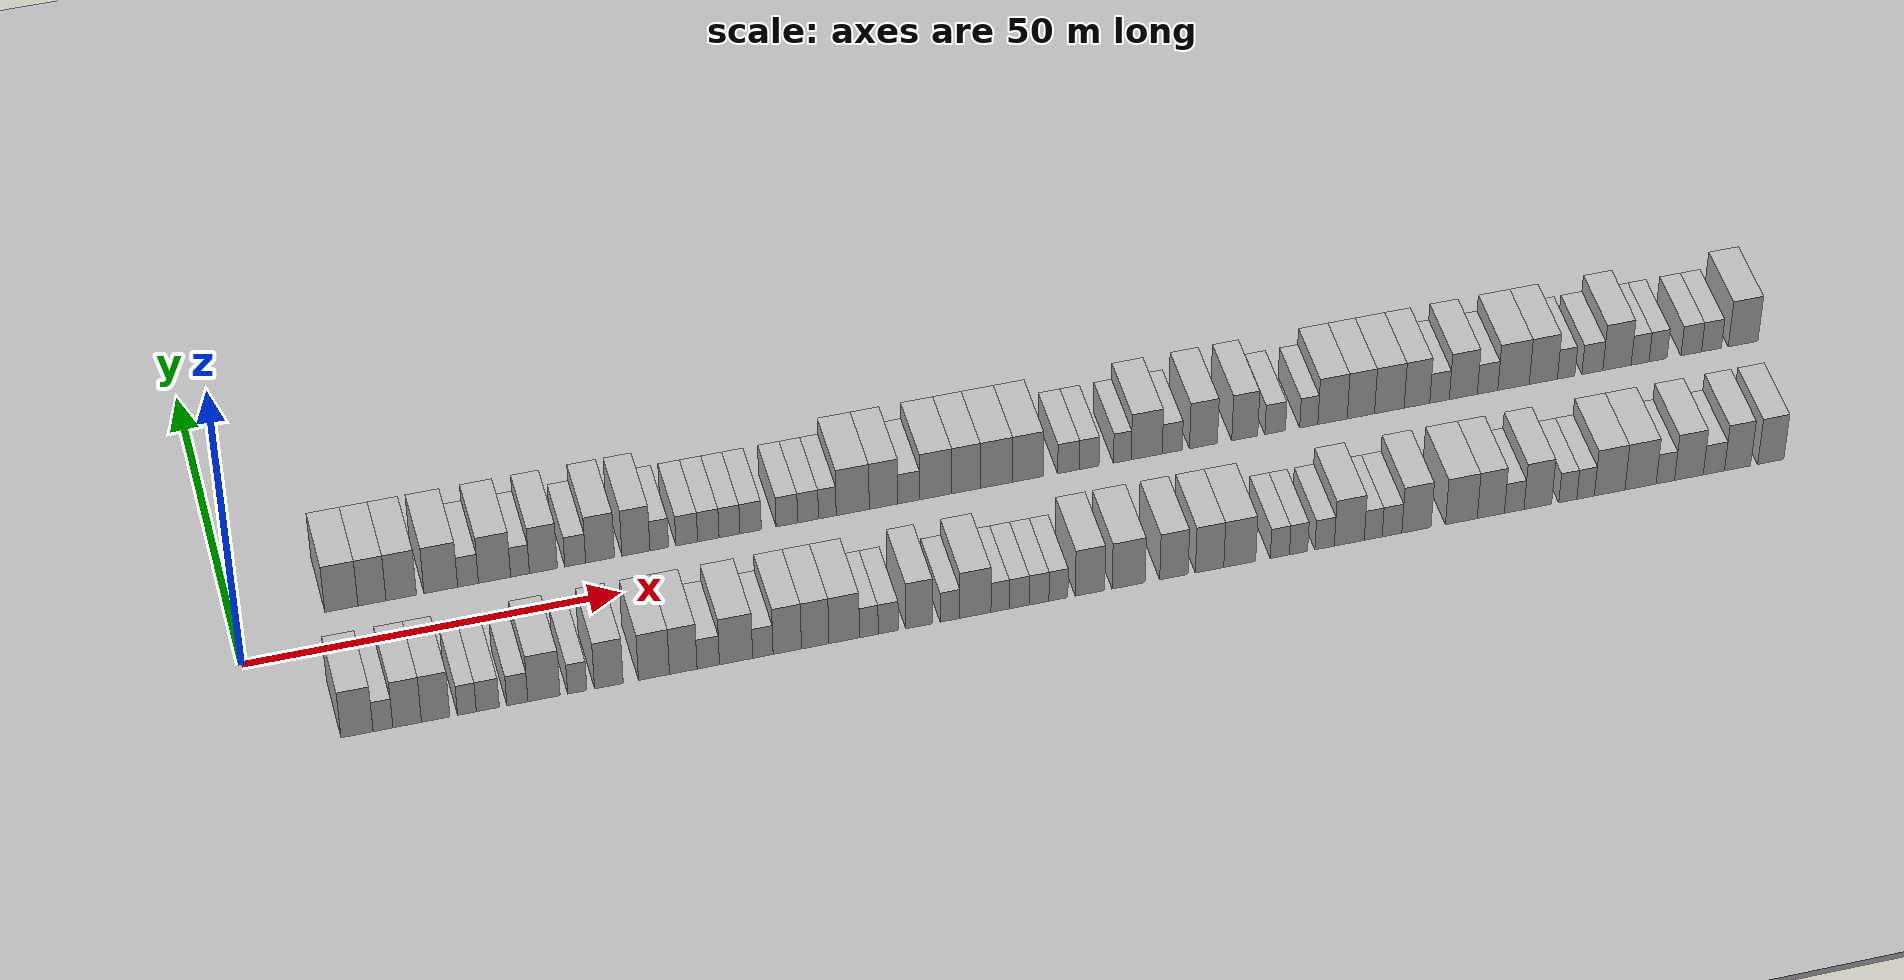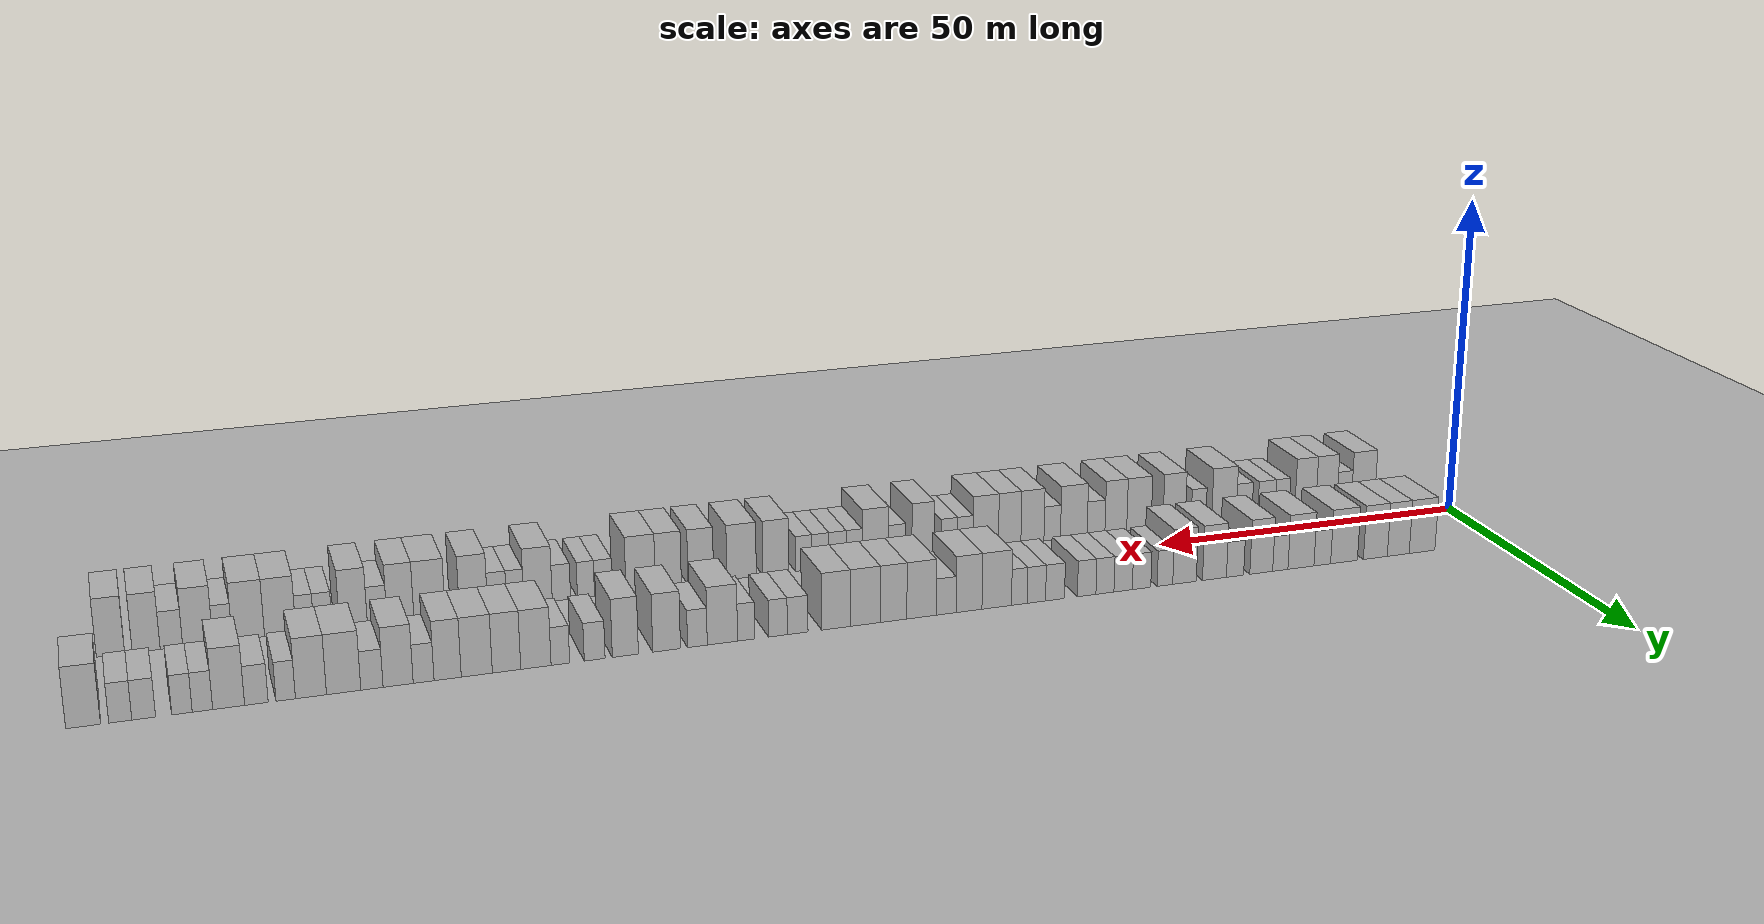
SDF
<?xml version="1.0" encoding="utf-8"?>

<sdf version="1.6">

   <world name="default">

      <gui fullscreen="0">

         <camera name="user_camera">

            <pose>-15 0 4.57585 0 0 0</pose>

            <view_controller>orbit</view_controller>

         </camera>

      </gui>

      <scene>

         <sky>

           <clouds>

             <speed>12</speed>

           </clouds>

         </sky>

         <ambient>0.4 0.4 0.4 1</ambient>

         <background>0.7 0.7 0.7 1</background>

         <shadows>1</shadows>

      </scene>

      <gravity>0 0 -9.8066</gravity>

      <magnetic_field>6e-06 2.3e-05 -4.2e-05</magnetic_field>

      <physics default="0" name="default_physics" type="ode">

         <ode>

            <solver>

               <type>quick</type>

               <iters>10</iters>

               <sor>1.0</sor>

               <use_dynamic_moi_rescaling>0</use_dynamic_moi_rescaling>

            </solver>

            <constraints>

               <cfm>0</cfm>

               <erp>0.2</erp>

               <contact_max_correcting_vel>100</contact_max_correcting_vel>

               <contact_surface_layer>0.001</contact_surface_layer>

            </constraints>

         </ode>

         <max_step_size>0.004</max_step_size>

         <real_time_factor>1</real_time_factor>

         <real_time_update_rate>250</real_time_update_rate>

      </physics>

      <light name="sun" type="directional">

         <cast_shadows>1</cast_shadows>

         <pose>0 0 10 0 0 0</pose>

         <diffuse>0.8 0.8 0.8 1</diffuse>

         <specular>0.2 0.2 0.2 1</specular>

         <attenuation>

            <range>1000</range>

            <constant>0.9</constant>

            <linear>0.01</linear>

            <quadratic>0.001</quadratic>

         </attenuation>

         <direction>-0.5 0.1 -0.9</direction>

      </light>

      <include>

         <name>ground_plane_1</name>

         <uri>model://HANNAS_ground_plane</uri>

         <pose>0 0 0  0 0 0</pose>

      </include>

      <include>

         <name>ground_plane_2</name>

         <uri>model://HANNAS_ground_plane</uri>

         <pose>100 0 0  0 0 0</pose>

      </include>

      <model name="building_1">

         <static>1</static>

         <pose frame="">14.1911 11.0000 0 0.000000 0.000000 1.570796</pose>

         <link name="link">

            <pose frame="">0 0 4.50 0 0 0</pose>

            <collision name="collision">

               <geometry>

                  <box>

                     <size>10.0000 4.3821 9.0000</size>

                  </box>

               </geometry>

               <max_contacts>10</max_contacts>

               <surface>

                  <contact>

                     <ode/>

                  </contact>

                  <bounce/>

                  <friction>

                     <torsional>

                        <ode/>

                     </torsional>

                     <ode/>

                  </friction>

               </surface>

            </collision>

            <visual name="visual">

               <cast_shadows>0</cast_shadows>

               <geometry>

                  <box>

                     <size>10.0000 4.3821 9.0000</size>

                  </box>

               </geometry>

               <material>

                  <script>

                     <uri>model://HANNAS_wall/materials/scripts</uri>

                     <uri>model://HANNAS_wall/materials/textures</uri>

                     <name>vrc/HANNAS_wall</name>

                  </script>

               </material>

            </visual>

            <self_collide>0</self_collide>

            <enable_wind>0</enable_wind>

            <kinematic>0</kinematic>

         </link>

      </model>

      <model name="building_2">

         <static>1</static>

         <pose frame="">18.2319 11.0000 0 0.000000 0.000000 1.570796</pose>

         <link name="link">

            <pose frame="">0 0 4.50 0 0 0</pose>

            <collision name="collision">

               <geometry>

                  <box>

                     <size>10.0000 3.6997 9.0000</size>

                  </box>

               </geometry>

               <max_contacts>10</max_contacts>

               <surface>

                  <contact>

                     <ode/>

                  </contact>

                  <bounce/>

                  <friction>

                     <torsional>

                        <ode/>

                     </torsional>

                     <ode/>

                  </friction>

               </surface>

            </collision>

            <visual name="visual">

               <cast_shadows>0</cast_shadows>

               <geometry>

                  <box>

                     <size>10.0000 3.6997 9.0000</size>

                  </box>

               </geometry>

               <material>

                  <script>

                     <uri>model://HANNAS_wall/materials/scripts</uri>

                     <uri>model://HANNAS_wall/materials/textures</uri>

                     <name>vrc/HANNAS_wall</name>

                  </script>

               </material>

            </visual>

            <self_collide>0</self_collide>

            <enable_wind>0</enable_wind>

            <kinematic>0</kinematic>

         </link>

      </model>

      <model name="building_3">

         <static>1</static>

         <pose frame="">22.0924 11.0000 0 0.000000 0.000000 1.570796</pose>

         <link name="link">

            <pose frame="">0 0 4.50 0 0 0</pose>

            <collision name="collision">

               <geometry>

                  <box>

                     <size>10.0000 4.0213 9.0000</size>

                  </box>

               </geometry>

               <max_contacts>10</max_contacts>

               <surface>

                  <contact>

                     <ode/>

                  </contact>

                  <bounce/>

                  <friction>

                     <torsional>

                        <ode/>

                     </torsional>

                     <ode/>

                  </friction>

               </surface>

            </collision>

            <visual name="visual">

               <cast_shadows>0</cast_shadows>

               <geometry>

                  <box>

                     <size>10.0000 4.0213 9.0000</size>

                  </box>

               </geometry>

               <material>

                  <script>

                     <uri>model://HANNAS_wall/materials/scripts</uri>

                     <uri>model://HANNAS_wall/materials/textures</uri>

                     <name>vrc/HANNAS_wall</name>

                  </script>

               </material>

            </visual>

            <self_collide>0</self_collide>

            <enable_wind>0</enable_wind>

            <kinematic>0</kinematic>

         </link>

      </model>

      <model name="building_4">

         <static>1</static>

         <pose frame="">27.3407 11.0000 0 0.000000 0.000000 1.570796</pose>

         <link name="link">

            <pose frame="">0 0 4.50 0 0 0</pose>

            <collision name="collision">

               <geometry>

                  <box>

                     <size>10.0000 4.4752 9.0000</size>

                  </box>

               </geometry>

               <max_contacts>10</max_contacts>

               <surface>

                  <contact>

                     <ode/>

                  </contact>

                  <bounce/>

                  <friction>

                     <torsional>

                        <ode/>

                     </torsional>

                     <ode/>

                  </friction>

               </surface>

            </collision>

            <visual name="visual">

               <cast_shadows>0</cast_shadows>

               <geometry>

                  <box>

                     <size>10.0000 4.4752 9.0000</size>

                  </box>

               </geometry>

               <material>

                  <script>

                     <uri>model://HANNAS_wall/materials/scripts</uri>

                     <uri>model://HANNAS_wall/materials/textures</uri>

                     <name>vrc/HANNAS_wall</name>

                  </script>

               </material>

            </visual>

            <self_collide>0</self_collide>

            <enable_wind>0</enable_wind>

            <kinematic>0</kinematic>

         </link>

      </model>

      <model name="building_5">

         <static>1</static>

         <pose frame="">30.9566 11.0000 0 0.000000 0.000000 1.570796</pose>

         <link name="link">

            <pose frame="">0 0 3.00 0 0 0</pose>

            <collision name="collision">

               <geometry>

                  <box>

                     <size>10.0000 2.7566 6.0000</size>

                  </box>

               </geometry>

               <max_contacts>10</max_contacts>

               <surface>

                  <contact>

                     <ode/>

                  </contact>

                  <bounce/>

                  <friction>

                     <torsional>

                        <ode/>

                     </torsional>

                     <ode/>

                  </friction>

               </surface>

            </collision>

            <visual name="visual">

               <cast_shadows>0</cast_shadows>

               <geometry>

                  <box>

                     <size>10.0000 2.7566 6.0000</size>

                  </box>

               </geometry>

               <material>

                  <script>

                     <uri>model://HANNAS_wall/materials/scripts</uri>

                     <uri>model://HANNAS_wall/materials/textures</uri>

                     <name>vrc/HANNAS_wall</name>

                  </script>

               </material>

            </visual>

            <self_collide>0</self_collide>

            <enable_wind>0</enable_wind>

            <kinematic>0</kinematic>

         </link>

      </model>

      <model name="building_6">

         <static>1</static>

         <pose frame="">34.4782 11.0000 0 0.000000 0.000000 1.570796</pose>

         <link name="link">

            <pose frame="">0 0 4.50 0 0 0</pose>

            <collision name="collision">

               <geometry>

                  <box>

                     <size>10.0000 4.2865 9.0000</size>

                  </box>

               </geometry>

               <max_contacts>10</max_contacts>

               <surface>

                  <contact>

                     <ode/>

                  </contact>

                  <bounce/>

                  <friction>

                     <torsional>

                        <ode/>

                     </torsional>

                     <ode/>

                  </friction>

               </surface>

            </collision>

            <visual name="visual">

               <cast_shadows>0</cast_shadows>

               <geometry>

                  <box>

                     <size>10.0000 4.2865 9.0000</size>

                  </box>

               </geometry>

               <material>

                  <script>

                     <uri>model://HANNAS_wall/materials/scripts</uri>

                     <uri>model://HANNAS_wall/materials/textures</uri>

                     <name>vrc/HANNAS_wall</name>

                  </script>

               </material>

            </visual>

            <self_collide>0</self_collide>

            <enable_wind>0</enable_wind>

            <kinematic>0</kinematic>

         </link>

      </model>

      <model name="building_7">

         <static>1</static>

         <pose frame="">37.8743 11.0000 0 0.000000 0.000000 1.570796</pose>

         <link name="link">

            <pose frame="">0 0 3.00 0 0 0</pose>

            <collision name="collision">

               <geometry>

                  <box>

                     <size>10.0000 2.5058 6.0000</size>

                  </box>

               </geometry>

               <max_contacts>10</max_contacts>

               <surface>

                  <contact>

                     <ode/>

                  </contact>

                  <bounce/>

                  <friction>

                     <torsional>

                        <ode/>

                     </torsional>

                     <ode/>

                  </friction>

               </surface>

            </collision>

            <visual name="visual">

               <cast_shadows>0</cast_shadows>

               <geometry>

                  <box>

                     <size>10.0000 2.5058 6.0000</size>

                  </box>

               </geometry>

               <material>

                  <script>

                     <uri>model://HANNAS_wall/materials/scripts</uri>

                     <uri>model://HANNAS_wall/materials/textures</uri>

                     <name>vrc/HANNAS_wall</name>

                  </script>

               </material>

            </visual>

            <self_collide>0</self_collide>

            <enable_wind>0</enable_wind>

            <kinematic>0</kinematic>

         </link>

      </model>

      <model name="building_8">

         <static>1</static>

         <pose frame="">40.9944 11.0000 0 0.000000 0.000000 1.570796</pose>

         <link name="link">

            <pose frame="">0 0 4.50 0 0 0</pose>

            <collision name="collision">

               <geometry>

                  <box>

                     <size>10.0000 3.7344 9.0000</size>

                  </box>

               </geometry>

               <max_contacts>10</max_contacts>

               <surface>

                  <contact>

                     <ode/>

                  </contact>

                  <bounce/>

                  <friction>

                     <torsional>

                        <ode/>

                     </torsional>

                     <ode/>

                  </friction>

               </surface>

            </collision>

            <visual name="visual">

               <cast_shadows>0</cast_shadows>

               <geometry>

                  <box>

                     <size>10.0000 3.7344 9.0000</size>

                  </box>

               </geometry>

               <material>

                  <script>

                     <uri>model://HANNAS_wall/materials/scripts</uri>

                     <uri>model://HANNAS_wall/materials/textures</uri>

                     <name>vrc/HANNAS_wall</name>

                  </script>

               </material>

            </visual>

            <self_collide>0</self_collide>

            <enable_wind>0</enable_wind>

            <kinematic>0</kinematic>

         </link>

      </model>

      <model name="building_9">

         <static>1</static>

         <pose frame="">45.2568 11.0000 0 0.000000 0.000000 1.570796</pose>

         <link name="link">

            <pose frame="">0 0 3.00 0 0 0</pose>

            <collision name="collision">

               <geometry>

                  <box>

                     <size>10.0000 2.7903 6.0000</size>

                  </box>

               </geometry>

               <max_contacts>10</max_contacts>

               <surface>

                  <contact>

                     <ode/>

                  </contact>

                  <bounce/>

                  <friction>

                     <torsional>

                        <ode/>

                     </torsional>

                     <ode/>

                  </friction>

               </surface>

            </collision>

            <visual name="visual">

               <cast_shadows>0</cast_shadows>

               <geometry>

                  <box>

                     <size>10.0000 2.7903 6.0000</size>

                  </box>

               </geometry>

               <material>

                  <script>

                     <uri>model://HANNAS_wall/materials/scripts</uri>

                     <uri>model://HANNAS_wall/materials/textures</uri>

                     <name>vrc/HANNAS_wall</name>

                  </script>

               </material>

            </visual>

            <self_collide>0</self_collide>

            <enable_wind>0</enable_wind>

            <kinematic>0</kinematic>

         </link>

      </model>

      <model name="building_10">

         <static>1</static>

         <pose frame="">48.5802 11.0000 0 0.000000 0.000000 1.570796</pose>

         <link name="link">

            <pose frame="">0 0 4.50 0 0 0</pose>

            <collision name="collision">

               <geometry>

                  <box>

                     <size>10.0000 3.8563 9.0000</size>

                  </box>

               </geometry>

               <max_contacts>10</max_contacts>

               <surface>

                  <contact>

                     <ode/>

                  </contact>

                  <bounce/>

                  <friction>

                     <torsional>

                        <ode/>

                     </torsional>

                     <ode/>

                  </friction>

               </surface>

            </collision>

            <visual name="visual">

               <cast_shadows>0</cast_shadows>

               <geometry>

                  <box>

                     <size>10.0000 3.8563 9.0000</size>

                  </box>

               </geometry>

               <material>

                  <script>

                     <uri>model://HANNAS_wall/materials/scripts</uri>

                     <uri>model://HANNAS_wall/materials/textures</uri>

                     <name>vrc/HANNAS_wall</name>

                  </script>

               </material>

            </visual>

            <self_collide>0</self_collide>

            <enable_wind>0</enable_wind>

            <kinematic>0</kinematic>

         </link>

      </model>

      <model name="building_11">

         <static>1</static>

         <pose frame="">53.3890 11.0000 0 0.000000 0.000000 1.570796</pose>

         <link name="link">

            <pose frame="">0 0 4.50 0 0 0</pose>

            <collision name="collision">

               <geometry>

                  <box>

                     <size>10.0000 3.7614 9.0000</size>

                  </box>

               </geometry>

               <max_contacts>10</max_contacts>

               <surface>

                  <contact>

                     <ode/>

                  </contact>

                  <bounce/>

                  <friction>

                     <torsional>

                        <ode/>

                     </torsional>

                     <ode/>

                  </friction>

               </surface>

            </collision>

            <visual name="visual">

               <cast_shadows>0</cast_shadows>

               <geometry>

                  <box>

                     <size>10.0000 3.7614 9.0000</size>

                  </box>

               </geometry>

               <material>

                  <script>

                     <uri>model://HANNAS_wall/materials/scripts</uri>

                     <uri>model://HANNAS_wall/materials/textures</uri>

                     <name>vrc/HANNAS_wall</name>

                  </script>

               </material>

            </visual>

            <self_collide>0</self_collide>

            <enable_wind>0</enable_wind>

            <kinematic>0</kinematic>

         </link>

      </model>

      <model name="building_12">

         <static>1</static>

         <pose frame="">56.5151 11.0000 0 0.000000 0.000000 1.570796</pose>

         <link name="link">

            <pose frame="">0 0 3.00 0 0 0</pose>

            <collision name="collision">

               <geometry>

                  <box>

                     <size>10.0000 2.4908 6.0000</size>

                  </box>

               </geometry>

               <max_contacts>10</max_contacts>

               <surface>

                  <contact>

                     <ode/>

                  </contact>

                  <bounce/>

                  <friction>

                     <torsional>

                        <ode/>

                     </torsional>

                     <ode/>

                  </friction>

               </surface>

            </collision>

            <visual name="visual">

               <cast_shadows>0</cast_shadows>

               <geometry>

                  <box>

                     <size>10.0000 2.4908 6.0000</size>

                  </box>

               </geometry>

               <material>

                  <script>

                     <uri>model://HANNAS_wall/materials/scripts</uri>

                     <uri>model://HANNAS_wall/materials/textures</uri>

                     <name>vrc/HANNAS_wall</name>

                  </script>

               </material>

            </visual>

            <self_collide>0</self_collide>

            <enable_wind>0</enable_wind>

            <kinematic>0</kinematic>

         </link>

      </model>

      <model name="building_13">

         <static>1</static>

         <pose frame="">60.2191 11.0000 0 0.000000 0.000000 1.570796</pose>

         <link name="link">

            <pose frame="">0 0 3.00 0 0 0</pose>

            <collision name="collision">

               <geometry>

                  <box>

                     <size>10.0000 2.9172 6.0000</size>

                  </box>

               </geometry>

               <max_contacts>10</max_contacts>

               <surface>

                  <contact>

                     <ode/>

                  </contact>

                  <bounce/>

                  <friction>

                     <torsional>

                        <ode/>

                     </torsional>

                     <ode/>

                  </friction>

               </surface>

            </collision>

            <visual name="visual">

               <cast_shadows>0</cast_shadows>

               <geometry>

                  <box>

                     <size>10.0000 2.9172 6.0000</size>

                  </box>

               </geometry>

               <material>

                  <script>

                     <uri>model://HANNAS_wall/materials/scripts</uri>

                     <uri>model://HANNAS_wall/materials/textures</uri>

                     <name>vrc/HANNAS_wall</name>

                  </script>

               </material>

            </visual>

            <self_collide>0</self_collide>

            <enable_wind>0</enable_wind>

            <kinematic>0</kinematic>

         </link>

      </model>

      <model name="building_14">

         <static>1</static>

         <pose frame="">63.1198 11.0000 0 0.000000 0.000000 1.570796</pose>

         <link name="link">

            <pose frame="">0 0 3.00 0 0 0</pose>

            <collision name="collision">

               <geometry>

                  <box>

                     <size>10.0000 2.8842 6.0000</size>

                  </box>

               </geometry>

               <max_contacts>10</max_contacts>

               <surface>

                  <contact>

                     <ode/>

                  </contact>

                  <bounce/>

                  <friction>

                     <torsional>

                        <ode/>

                     </torsional>

                     <ode/>

                  </friction>

               </surface>

            </collision>

            <visual name="visual">

               <cast_shadows>0</cast_shadows>

               <geometry>

                  <box>

                     <size>10.0000 2.8842 6.0000</size>

                  </box>

               </geometry>

               <material>

                  <script>

                     <uri>model://HANNAS_wall/materials/scripts</uri>

                     <uri>model://HANNAS_wall/materials/textures</uri>

                     <name>vrc/HANNAS_wall</name>

                  </script>

               </material>

            </visual>

            <self_collide>0</self_collide>

            <enable_wind>0</enable_wind>

            <kinematic>0</kinematic>

         </link>

      </model>

      <model name="building_15">

         <static>1</static>

         <pose frame="">65.9718 11.0000 0 0.000000 0.000000 1.570796</pose>

         <link name="link">

            <pose frame="">0 0 3.00 0 0 0</pose>

            <collision name="collision">

               <geometry>

                  <box>

                     <size>10.0000 2.8198 6.0000</size>

                  </box>

               </geometry>

               <max_contacts>10</max_contacts>

               <surface>

                  <contact>

                     <ode/>

                  </contact>

                  <bounce/>

                  <friction>

                     <torsional>

                        <ode/>

                     </torsional>

                     <ode/>

                  </friction>

               </surface>

            </collision>

            <visual name="visual">

               <cast_shadows>0</cast_shadows>

               <geometry>

                  <box>

                     <size>10.0000 2.8198 6.0000</size>

                  </box>

               </geometry>

               <material>

                  <script>

                     <uri>model://HANNAS_wall/materials/scripts</uri>

                     <uri>model://HANNAS_wall/materials/textures</uri>

                     <name>vrc/HANNAS_wall</name>

                  </script>

               </material>

            </visual>

            <self_collide>0</self_collide>

            <enable_wind>0</enable_wind>

            <kinematic>0</kinematic>

         </link>

      </model>

      <model name="building_16">

         <static>1</static>

         <pose frame="">68.8249 11.0000 0 0.000000 0.000000 1.570796</pose>

         <link name="link">

            <pose frame="">0 0 3.00 0 0 0</pose>

            <collision name="collision">

               <geometry>

                  <box>

                     <size>10.0000 2.8863 6.0000</size>

                  </box>

               </geometry>

               <max_contacts>10</max_contacts>

               <surface>

                  <contact>

                     <ode/>

                  </contact>

                  <bounce/>

                  <friction>

                     <torsional>

                        <ode/>

                     </torsional>

                     <ode/>

                  </friction>

               </surface>

            </collision>

            <visual name="visual">

               <cast_shadows>0</cast_shadows>

               <geometry>

                  <box>

                     <size>10.0000 2.8863 6.0000</size>

                  </box>

               </geometry>

               <material>

                  <script>

                     <uri>model://HANNAS_wall/materials/scripts</uri>

                     <uri>model://HANNAS_wall/materials/textures</uri>

                     <name>vrc/HANNAS_wall</name>

                  </script>

               </material>

            </visual>

            <self_collide>0</self_collide>

            <enable_wind>0</enable_wind>

            <kinematic>0</kinematic>

         </link>

      </model>

      <model name="building_17">

         <static>1</static>

         <pose frame="">73.7291 11.0000 0 0.000000 0.000000 1.570796</pose>

         <link name="link">

            <pose frame="">0 0 3.00 0 0 0</pose>

            <collision name="collision">

               <geometry>

                  <box>

                     <size>10.0000 2.9221 6.0000</size>

                  </box>

               </geometry>

               <max_contacts>10</max_contacts>

               <surface>

                  <contact>

                     <ode/>

                  </contact>

                  <bounce/>

                  <friction>

                     <torsional>

                        <ode/>

                     </torsional>

                     <ode/>

                  </friction>

               </surface>

            </collision>

            <visual name="visual">

               <cast_shadows>0</cast_shadows>

               <geometry>

                  <box>

                     <size>10.0000 2.9221 6.0000</size>

                  </box>

               </geometry>

               <material>

                  <script>

                     <uri>model://HANNAS_wall/materials/scripts</uri>

                     <uri>model://HANNAS_wall/materials/textures</uri>

                     <name>vrc/HANNAS_wall</name>

                  </script>

               </material>

            </visual>

            <self_collide>0</self_collide>

            <enable_wind>0</enable_wind>

            <kinematic>0</kinematic>

         </link>

      </model>

      <model name="building_18">

         <static>1</static>

         <pose frame="">76.6007 11.0000 0 0.000000 0.000000 1.570796</pose>

         <link name="link">

            <pose frame="">0 0 3.00 0 0 0</pose>

            <collision name="collision">

               <geometry>

                  <box>

                     <size>10.0000 2.8211 6.0000</size>

                  </box>

               </geometry>

               <max_contacts>10</max_contacts>

               <surface>

                  <contact>

                     <ode/>

                  </contact>

                  <bounce/>

                  <friction>

                     <torsional>

                        <ode/>

                     </torsional>

                     <ode/>

                  </friction>

               </surface>

            </collision>

            <visual name="visual">

               <cast_shadows>0</cast_shadows>

               <geometry>

                  <box>

                     <size>10.0000 2.8211 6.0000</size>

                  </box>

               </geometry>

               <material>

                  <script>

                     <uri>model://HANNAS_wall/materials/scripts</uri>

                     <uri>model://HANNAS_wall/materials/textures</uri>

                     <name>vrc/HANNAS_wall</name>

                  </script>

               </material>

            </visual>

            <self_collide>0</self_collide>

            <enable_wind>0</enable_wind>

            <kinematic>0</kinematic>

         </link>

      </model>

      <model name="building_19">

         <static>1</static>

         <pose frame="">79.2155 11.0000 0 0.000000 0.000000 1.570796</pose>

         <link name="link">

            <pose frame="">0 0 3.00 0 0 0</pose>

            <collision name="collision">

               <geometry>

                  <box>

                     <size>10.0000 2.4084 6.0000</size>

                  </box>

               </geometry>

               <max_contacts>10</max_contacts>

               <surface>

                  <contact>

                     <ode/>

                  </contact>

                  <bounce/>

                  <friction>

                     <torsional>

                        <ode/>

                     </torsional>

                     <ode/>

                  </friction>

               </surface>

            </collision>

            <visual name="visual">

               <cast_shadows>0</cast_shadows>

               <geometry>

                  <box>

                     <size>10.0000 2.4084 6.0000</size>

                  </box>

               </geometry>

               <material>

                  <script>

                     <uri>model://HANNAS_wall/materials/scripts</uri>

                     <uri>model://HANNAS_wall/materials/textures</uri>

                     <name>vrc/HANNAS_wall</name>

                  </script>

               </material>

            </visual>

            <self_collide>0</self_collide>

            <enable_wind>0</enable_wind>

            <kinematic>0</kinematic>

         </link>

      </model>

      <model name="building_20">

         <static>1</static>

         <pose frame="">82.6691 11.0000 0 0.000000 0.000000 1.570796</pose>

         <link name="link">

            <pose frame="">0 0 4.50 0 0 0</pose>

            <collision name="collision">

               <geometry>

                  <box>

                     <size>10.0000 4.4989 9.0000</size>

                  </box>

               </geometry>

               <max_contacts>10</max_contacts>

               <surface>

                  <contact>

                     <ode/>

                  </contact>

                  <bounce/>

                  <friction>

                     <torsional>

                        <ode/>

                     </torsional>

                     <ode/>

                  </friction>

               </surface>

            </collision>

            <visual name="visual">

               <cast_shadows>0</cast_shadows>

               <geometry>

                  <box>

                     <size>10.0000 4.4989 9.0000</size>

                  </box>

               </geometry>

               <material>

                  <script>

                     <uri>model://HANNAS_wall/materials/scripts</uri>

                     <uri>model://HANNAS_wall/materials/textures</uri>

                     <name>vrc/HANNAS_wall</name>

                  </script>

               </material>

            </visual>

            <self_collide>0</self_collide>

            <enable_wind>0</enable_wind>

            <kinematic>0</kinematic>

         </link>

      </model>

      <model name="building_21">

         <static>1</static>

         <pose frame="">86.8722 11.0000 0 0.000000 0.000000 1.570796</pose>

         <link name="link">

            <pose frame="">0 0 4.50 0 0 0</pose>

            <collision name="collision">

               <geometry>

                  <box>

                     <size>10.0000 3.9072 9.0000</size>

                  </box>

               </geometry>

               <max_contacts>10</max_contacts>

               <surface>

                  <contact>

                     <ode/>

                  </contact>

                  <bounce/>

                  <friction>

                     <torsional>

                        <ode/>

                     </torsional>

                     <ode/>

                  </friction>

               </surface>

            </collision>

            <visual name="visual">

               <cast_shadows>0</cast_shadows>

               <geometry>

                  <box>

                     <size>10.0000 3.9072 9.0000</size>

                  </box>

               </geometry>

               <material>

                  <script>

                     <uri>model://HANNAS_wall/materials/scripts</uri>

                     <uri>model://HANNAS_wall/materials/textures</uri>

                     <name>vrc/HANNAS_wall</name>

                  </script>

               </material>

            </visual>

            <self_collide>0</self_collide>

            <enable_wind>0</enable_wind>

            <kinematic>0</kinematic>

         </link>

      </model>

      <model name="building_22">

         <static>1</static>

         <pose frame="">90.3051 11.0000 0 0.000000 0.000000 1.570796</pose>

         <link name="link">

            <pose frame="">0 0 3.00 0 0 0</pose>

            <collision name="collision">

               <geometry>

                  <box>

                     <size>10.0000 2.9587 6.0000</size>

                  </box>

               </geometry>

               <max_contacts>10</max_contacts>

               <surface>

                  <contact>

                     <ode/>

                  </contact>

                  <bounce/>

                  <friction>

                     <torsional>

                        <ode/>

                     </torsional>

                     <ode/>

                  </friction>

               </surface>

            </collision>

            <visual name="visual">

               <cast_shadows>0</cast_shadows>

               <geometry>

                  <box>

                     <size>10.0000 2.9587 6.0000</size>

                  </box>

               </geometry>

               <material>

                  <script>

                     <uri>model://HANNAS_wall/materials/scripts</uri>

                     <uri>model://HANNAS_wall/materials/textures</uri>

                     <name>vrc/HANNAS_wall</name>

                  </script>

               </material>

            </visual>

            <self_collide>0</self_collide>

            <enable_wind>0</enable_wind>

            <kinematic>0</kinematic>

         </link>

      </model>

      <model name="building_23">

         <static>1</static>

         <pose frame="">93.9879 11.0000 0 0.000000 0.000000 1.570796</pose>

         <link name="link">

            <pose frame="">0 0 4.50 0 0 0</pose>

            <collision name="collision">

               <geometry>

                  <box>

                     <size>10.0000 4.4069 9.0000</size>

                  </box>

               </geometry>

               <max_contacts>10</max_contacts>

               <surface>

                  <contact>

                     <ode/>

                  </contact>

                  <bounce/>

                  <friction>

                     <torsional>

                        <ode/>

                     </torsional>

                     <ode/>

                  </friction>

               </surface>

            </collision>

            <visual name="visual">

               <cast_shadows>0</cast_shadows>

               <geometry>

                  <box>

                     <size>10.0000 4.4069 9.0000</size>

                  </box>

               </geometry>

               <material>

                  <script>

                     <uri>model://HANNAS_wall/materials/scripts</uri>

                     <uri>model://HANNAS_wall/materials/textures</uri>

                     <name>vrc/HANNAS_wall</name>

                  </script>

               </material>

            </visual>

            <self_collide>0</self_collide>

            <enable_wind>0</enable_wind>

            <kinematic>0</kinematic>

         </link>

      </model>

      <model name="building_24">

         <static>1</static>

         <pose frame="">98.1364 11.0000 0 0.000000 0.000000 1.570796</pose>

         <link name="link">

            <pose frame="">0 0 4.50 0 0 0</pose>

            <collision name="collision">

               <geometry>

                  <box>

                     <size>10.0000 3.8901 9.0000</size>

                  </box>

               </geometry>

               <max_contacts>10</max_contacts>

               <surface>

                  <contact>

                     <ode/>

                  </contact>

                  <bounce/>

                  <friction>

                     <torsional>

                        <ode/>

                     </torsional>

                     <ode/>

                  </friction>

               </surface>

            </collision>

            <visual name="visual">

               <cast_shadows>0</cast_shadows>

               <geometry>

                  <box>

                     <size>10.0000 3.8901 9.0000</size>

                  </box>

               </geometry>

               <material>

                  <script>

                     <uri>model://HANNAS_wall/materials/scripts</uri>

                     <uri>model://HANNAS_wall/materials/textures</uri>

                     <name>vrc/HANNAS_wall</name>

                  </script>

               </material>

            </visual>

            <self_collide>0</self_collide>

            <enable_wind>0</enable_wind>

            <kinematic>0</kinematic>

         </link>

      </model>

      <model name="building_25">

         <static>1</static>

         <pose frame="">102.2956 11.0000 0 0.000000 0.000000 1.570796</pose>

         <link name="link">

            <pose frame="">0 0 4.50 0 0 0</pose>

            <collision name="collision">

               <geometry>

                  <box>

                     <size>10.0000 4.4283 9.0000</size>

                  </box>

               </geometry>

               <max_contacts>10</max_contacts>

               <surface>

                  <contact>

                     <ode/>

                  </contact>

                  <bounce/>

                  <friction>

                     <torsional>

                        <ode/>

                     </torsional>

                     <ode/>

                  </friction>

               </surface>

            </collision>

            <visual name="visual">

               <cast_shadows>0</cast_shadows>

               <geometry>

                  <box>

                     <size>10.0000 4.4283 9.0000</size>

                  </box>

               </geometry>

               <material>

                  <script>

                     <uri>model://HANNAS_wall/materials/scripts</uri>

                     <uri>model://HANNAS_wall/materials/textures</uri>

                     <name>vrc/HANNAS_wall</name>

                  </script>

               </material>

            </visual>

            <self_collide>0</self_collide>

            <enable_wind>0</enable_wind>

            <kinematic>0</kinematic>

         </link>

      </model>

      <model name="building_26">

         <static>1</static>

         <pose frame="">106.6128 11.0000 0 0.000000 0.000000 1.570796</pose>

         <link name="link">

            <pose frame="">0 0 4.50 0 0 0</pose>

            <collision name="collision">

               <geometry>

                  <box>

                     <size>10.0000 4.2061 9.0000</size>

                  </box>

               </geometry>

               <max_contacts>10</max_contacts>

               <surface>

                  <contact>

                     <ode/>

                  </contact>

                  <bounce/>

                  <friction>

                     <torsional>

                        <ode/>

                     </torsional>

                     <ode/>

                  </friction>

               </surface>

            </collision>

            <visual name="visual">

               <cast_shadows>0</cast_shadows>

               <geometry>

                  <box>

                     <size>10.0000 4.2061 9.0000</size>

                  </box>

               </geometry>

               <material>

                  <script>

                     <uri>model://HANNAS_wall/materials/scripts</uri>

                     <uri>model://HANNAS_wall/materials/textures</uri>

                     <name>vrc/HANNAS_wall</name>

                  </script>

               </material>

            </visual>

            <self_collide>0</self_collide>

            <enable_wind>0</enable_wind>

            <kinematic>0</kinematic>

         </link>

      </model>

      <model name="building_27">

         <static>1</static>

         <pose frame="">112.2107 11.0000 0 0.000000 0.000000 1.570796</pose>

         <link name="link">

            <pose frame="">0 0 3.00 0 0 0</pose>

            <collision name="collision">

               <geometry>

                  <box>

                     <size>10.0000 2.9899 6.0000</size>

                  </box>

               </geometry>

               <max_contacts>10</max_contacts>

               <surface>

                  <contact>

                     <ode/>

                  </contact>

                  <bounce/>

                  <friction>

                     <torsional>

                        <ode/>

                     </torsional>

                     <ode/>

                  </friction>

               </surface>

            </collision>

            <visual name="visual">

               <cast_shadows>0</cast_shadows>

               <geometry>

                  <box>

                     <size>10.0000 2.9899 6.0000</size>

                  </box>

               </geometry>

               <material>

                  <script>

                     <uri>model://HANNAS_wall/materials/scripts</uri>

                     <uri>model://HANNAS_wall/materials/textures</uri>

                     <name>vrc/HANNAS_wall</name>

                  </script>

               </material>

            </visual>

            <self_collide>0</self_collide>

            <enable_wind>0</enable_wind>

            <kinematic>0</kinematic>

         </link>

      </model>

      <model name="building_28">

         <static>1</static>

         <pose frame="">115.0543 11.0000 0 0.000000 0.000000 1.570796</pose>

         <link name="link">

            <pose frame="">0 0 3.00 0 0 0</pose>

            <collision name="collision">

               <geometry>

                  <box>

                     <size>10.0000 2.6972 6.0000</size>

                  </box>

               </geometry>

               <max_contacts>10</max_contacts>

               <surface>

                  <contact>

                     <ode/>

                  </contact>

                  <bounce/>

                  <friction>

                     <torsional>

                        <ode/>

                     </torsional>

                     <ode/>

                  </friction>

               </surface>

            </collision>

            <visual name="visual">

               <cast_shadows>0</cast_shadows>

               <geometry>

                  <box>

                     <size>10.0000 2.6972 6.0000</size>

                  </box>

               </geometry>

               <material>

                  <script>

                     <uri>model://HANNAS_wall/materials/scripts</uri>

                     <uri>model://HANNAS_wall/materials/textures</uri>

                     <name>vrc/HANNAS_wall</name>

                  </script>

               </material>

            </visual>

            <self_collide>0</self_collide>

            <enable_wind>0</enable_wind>

            <kinematic>0</kinematic>

         </link>

      </model>

      <model name="building_29">

         <static>1</static>

         <pose frame="">119.6240 11.0000 0 0.000000 0.000000 1.570796</pose>

         <link name="link">

            <pose frame="">0 0 3.00 0 0 0</pose>

            <collision name="collision">

               <geometry>

                  <box>

                     <size>10.0000 2.4422 6.0000</size>

                  </box>

               </geometry>

               <max_contacts>10</max_contacts>

               <surface>

                  <contact>

                     <ode/>

                  </contact>

                  <bounce/>

                  <friction>

                     <torsional>

                        <ode/>

                     </torsional>

                     <ode/>

                  </friction>

               </surface>

            </collision>

            <visual name="visual">

               <cast_shadows>0</cast_shadows>

               <geometry>

                  <box>

                     <size>10.0000 2.4422 6.0000</size>

                  </box>

               </geometry>

               <material>

                  <script>

                     <uri>model://HANNAS_wall/materials/scripts</uri>

                     <uri>model://HANNAS_wall/materials/textures</uri>

                     <name>vrc/HANNAS_wall</name>

                  </script>

               </material>

            </visual>

            <self_collide>0</self_collide>

            <enable_wind>0</enable_wind>

            <kinematic>0</kinematic>

         </link>

      </model>

      <model name="building_30">

         <static>1</static>

         <pose frame="">122.9964 11.0000 0 0.000000 0.000000 1.570796</pose>

         <link name="link">

            <pose frame="">0 0 4.50 0 0 0</pose>

            <collision name="collision">

               <geometry>

                  <box>

                     <size>10.0000 4.3027 9.0000</size>

                  </box>

               </geometry>

               <max_contacts>10</max_contacts>

               <surface>

                  <contact>

                     <ode/>

                  </contact>

                  <bounce/>

                  <friction>

                     <torsional>

                        <ode/>

                     </torsional>

                     <ode/>

                  </friction>

               </surface>

            </collision>

            <visual name="visual">

               <cast_shadows>0</cast_shadows>

               <geometry>

                  <box>

                     <size>10.0000 4.3027 9.0000</size>

                  </box>

               </geometry>

               <material>

                  <script>

                     <uri>model://HANNAS_wall/materials/scripts</uri>

                     <uri>model://HANNAS_wall/materials/textures</uri>

                     <name>vrc/HANNAS_wall</name>

                  </script>

               </material>

            </visual>

            <self_collide>0</self_collide>

            <enable_wind>0</enable_wind>

            <kinematic>0</kinematic>

         </link>

      </model>

      <model name="building_31">

         <static>1</static>

         <pose frame="">126.5361 11.0000 0 0.000000 0.000000 1.570796</pose>

         <link name="link">

            <pose frame="">0 0 3.00 0 0 0</pose>

            <collision name="collision">

               <geometry>

                  <box>

                     <size>10.0000 2.7767 6.0000</size>

                  </box>

               </geometry>

               <max_contacts>10</max_contacts>

               <surface>

                  <contact>

                     <ode/>

                  </contact>

                  <bounce/>

                  <friction>

                     <torsional>

                        <ode/>

                     </torsional>

                     <ode/>

                  </friction>

               </surface>

            </collision>

            <visual name="visual">

               <cast_shadows>0</cast_shadows>

               <geometry>

                  <box>

                     <size>10.0000 2.7767 6.0000</size>

                  </box>

               </geometry>

               <material>

                  <script>

                     <uri>model://HANNAS_wall/materials/scripts</uri>

                     <uri>model://HANNAS_wall/materials/textures</uri>

                     <name>vrc/HANNAS_wall</name>

                  </script>

               </material>

            </visual>

            <self_collide>0</self_collide>

            <enable_wind>0</enable_wind>

            <kinematic>0</kinematic>

         </link>

      </model>

      <model name="building_32">

         <static>1</static>

         <pose frame="">130.8658 11.0000 0 0.000000 0.000000 1.570796</pose>

         <link name="link">

            <pose frame="">0 0 4.50 0 0 0</pose>

            <collision name="collision">

               <geometry>

                  <box>

                     <size>10.0000 3.8825 9.0000</size>

                  </box>

               </geometry>

               <max_contacts>10</max_contacts>

               <surface>

                  <contact>

                     <ode/>

                  </contact>

                  <bounce/>

                  <friction>

                     <torsional>

                        <ode/>

                     </torsional>

                     <ode/>

                  </friction>

               </surface>

            </collision>

            <visual name="visual">

               <cast_shadows>0</cast_shadows>

               <geometry>

                  <box>

                     <size>10.0000 3.8825 9.0000</size>

                  </box>

               </geometry>

               <material>

                  <script>

                     <uri>model://HANNAS_wall/materials/scripts</uri>

                     <uri>model://HANNAS_wall/materials/textures</uri>

                     <name>vrc/HANNAS_wall</name>

                  </script>

               </material>

            </visual>

            <self_collide>0</self_collide>

            <enable_wind>0</enable_wind>

            <kinematic>0</kinematic>

         </link>

      </model>

      <model name="building_33">

         <static>1</static>

         <pose frame="">136.6136 11.0000 0 0.000000 0.000000 1.570796</pose>

         <link name="link">

            <pose frame="">0 0 4.50 0 0 0</pose>

            <collision name="collision">

               <geometry>

                  <box>

                     <size>10.0000 3.6131 9.0000</size>

                  </box>

               </geometry>

               <max_contacts>10</max_contacts>

               <surface>

                  <contact>

                     <ode/>

                  </contact>

                  <bounce/>

                  <friction>

                     <torsional>

                        <ode/>

                     </torsional>

                     <ode/>

                  </friction>

               </surface>

            </collision>

            <visual name="visual">

               <cast_shadows>0</cast_shadows>

               <geometry>

                  <box>

                     <size>10.0000 3.6131 9.0000</size>

                  </box>

               </geometry>

               <material>

                  <script>

                     <uri>model://HANNAS_wall/materials/scripts</uri>

                     <uri>model://HANNAS_wall/materials/textures</uri>

                     <name>vrc/HANNAS_wall</name>

                  </script>

               </material>

            </visual>

            <self_collide>0</self_collide>

            <enable_wind>0</enable_wind>

            <kinematic>0</kinematic>

         </link>

      </model>

      <model name="building_34">

         <static>1</static>

         <pose frame="">140.8536 11.0000 0 0.000000 0.000000 1.570796</pose>

         <link name="link">

            <pose frame="">0 0 3.00 0 0 0</pose>

            <collision name="collision">

               <geometry>

                  <box>

                     <size>10.0000 2.8669 6.0000</size>

                  </box>

               </geometry>

               <max_contacts>10</max_contacts>

               <surface>

                  <contact>

                     <ode/>

                  </contact>

                  <bounce/>

                  <friction>

                     <torsional>

                        <ode/>

                     </torsional>

                     <ode/>

                  </friction>

               </surface>

            </collision>

            <visual name="visual">

               <cast_shadows>0</cast_shadows>

               <geometry>

                  <box>

                     <size>10.0000 2.8669 6.0000</size>

                  </box>

               </geometry>

               <material>

                  <script>

                     <uri>model://HANNAS_wall/materials/scripts</uri>

                     <uri>model://HANNAS_wall/materials/textures</uri>

                     <name>vrc/HANNAS_wall</name>

                  </script>

               </material>

            </visual>

            <self_collide>0</self_collide>

            <enable_wind>0</enable_wind>

            <kinematic>0</kinematic>

         </link>

      </model>

      <model name="building_35">

         <static>1</static>

         <pose frame="">145.5535 11.0000 0 0.000000 0.000000 1.570796</pose>

         <link name="link">

            <pose frame="">0 0 3.00 0 0 0</pose>

            <collision name="collision">

               <geometry>

                  <box>

                     <size>10.0000 2.5329 6.0000</size>

                  </box>

               </geometry>

               <max_contacts>10</max_contacts>

               <surface>

                  <contact>

                     <ode/>

                  </contact>

                  <bounce/>

                  <friction>

                     <torsional>

                        <ode/>

                     </torsional>

                     <ode/>

                  </friction>

               </surface>

            </collision>

            <visual name="visual">

               <cast_shadows>0</cast_shadows>

               <geometry>

                  <box>

                     <size>10.0000 2.5329 6.0000</size>

                  </box>

               </geometry>

               <material>

                  <script>

                     <uri>model://HANNAS_wall/materials/scripts</uri>

                     <uri>model://HANNAS_wall/materials/textures</uri>

                     <name>vrc/HANNAS_wall</name>

                  </script>

               </material>

            </visual>

            <self_collide>0</self_collide>

            <enable_wind>0</enable_wind>

            <kinematic>0</kinematic>

         </link>

      </model>

      <model name="building_36">

         <static>1</static>

         <pose frame="">148.8755 11.0000 0 0.000000 0.000000 1.570796</pose>

         <link name="link">

            <pose frame="">0 0 4.50 0 0 0</pose>

            <collision name="collision">

               <geometry>

                  <box>

                     <size>10.0000 4.1110 9.0000</size>

                  </box>

               </geometry>

               <max_contacts>10</max_contacts>

               <surface>

                  <contact>

                     <ode/>

                  </contact>

                  <bounce/>

                  <friction>

                     <torsional>

                        <ode/>

                     </torsional>

                     <ode/>

                  </friction>

               </surface>

            </collision>

            <visual name="visual">

               <cast_shadows>0</cast_shadows>

               <geometry>

                  <box>

                     <size>10.0000 4.1110 9.0000</size>

                  </box>

               </geometry>

               <material>

                  <script>

                     <uri>model://HANNAS_wall/materials/scripts</uri>

                     <uri>model://HANNAS_wall/materials/textures</uri>

                     <name>vrc/HANNAS_wall</name>

                  </script>

               </material>

            </visual>

            <self_collide>0</self_collide>

            <enable_wind>0</enable_wind>

            <kinematic>0</kinematic>

         </link>

      </model>

      <model name="building_37">

         <static>1</static>

         <pose frame="">152.8462 11.0000 0 0.000000 0.000000 1.570796</pose>

         <link name="link">

            <pose frame="">0 0 4.50 0 0 0</pose>

            <collision name="collision">

               <geometry>

                  <box>

                     <size>10.0000 3.8305 9.0000</size>

                  </box>

               </geometry>

               <max_contacts>10</max_contacts>

               <surface>

                  <contact>

                     <ode/>

                  </contact>

                  <bounce/>

                  <friction>

                     <torsional>

                        <ode/>

                     </torsional>

                     <ode/>

                  </friction>

               </surface>

            </collision>

            <visual name="visual">

               <cast_shadows>0</cast_shadows>

               <geometry>

                  <box>

                     <size>10.0000 3.8305 9.0000</size>

                  </box>

               </geometry>

               <material>

                  <script>

                     <uri>model://HANNAS_wall/materials/scripts</uri>

                     <uri>model://HANNAS_wall/materials/textures</uri>

                     <name>vrc/HANNAS_wall</name>

                  </script>

               </material>

            </visual>

            <self_collide>0</self_collide>

            <enable_wind>0</enable_wind>

            <kinematic>0</kinematic>

         </link>

      </model>

      <model name="building_38">

         <static>1</static>

         <pose frame="">156.8395 11.0000 0 0.000000 0.000000 1.570796</pose>

         <link name="link">

            <pose frame="">0 0 4.50 0 0 0</pose>

            <collision name="collision">

               <geometry>

                  <box>

                     <size>10.0000 4.1561 9.0000</size>

                  </box>

               </geometry>

               <max_contacts>10</max_contacts>

               <surface>

                  <contact>

                     <ode/>

                  </contact>

                  <bounce/>

                  <friction>

                     <torsional>

                        <ode/>

                     </torsional>

                     <ode/>

                  </friction>

               </surface>

            </collision>

            <visual name="visual">

               <cast_shadows>0</cast_shadows>

               <geometry>

                  <box>

                     <size>10.0000 4.1561 9.0000</size>

                  </box>

               </geometry>

               <material>

                  <script>

                     <uri>model://HANNAS_wall/materials/scripts</uri>

                     <uri>model://HANNAS_wall/materials/textures</uri>

                     <name>vrc/HANNAS_wall</name>

                  </script>

               </material>

            </visual>

            <self_collide>0</self_collide>

            <enable_wind>0</enable_wind>

            <kinematic>0</kinematic>

         </link>

      </model>

      <model name="building_39">

         <static>1</static>

         <pose frame="">160.7221 11.0000 0 0.000000 0.000000 1.570796</pose>

         <link name="link">

            <pose frame="">0 0 4.50 0 0 0</pose>

            <collision name="collision">

               <geometry>

                  <box>

                     <size>10.0000 3.6091 9.0000</size>

                  </box>

               </geometry>

               <max_contacts>10</max_contacts>

               <surface>

                  <contact>

                     <ode/>

                  </contact>

                  <bounce/>

                  <friction>

                     <torsional>

                        <ode/>

                     </torsional>

                     <ode/>

                  </friction>

               </surface>

            </collision>

            <visual name="visual">

               <cast_shadows>0</cast_shadows>

               <geometry>

                  <box>

                     <size>10.0000 3.6091 9.0000</size>

                  </box>

               </geometry>

               <material>

                  <script>

                     <uri>model://HANNAS_wall/materials/scripts</uri>

                     <uri>model://HANNAS_wall/materials/textures</uri>

                     <name>vrc/HANNAS_wall</name>

                  </script>

               </material>

            </visual>

            <self_collide>0</self_collide>

            <enable_wind>0</enable_wind>

            <kinematic>0</kinematic>

         </link>

      </model>

      <model name="building_40">

         <static>1</static>

         <pose frame="">163.9028 11.0000 0 0.000000 0.000000 1.570796</pose>

         <link name="link">

            <pose frame="">0 0 3.00 0 0 0</pose>

            <collision name="collision">

               <geometry>

                  <box>

                     <size>10.0000 2.7522 6.0000</size>

                  </box>

               </geometry>

               <max_contacts>10</max_contacts>

               <surface>

                  <contact>

                     <ode/>

                  </contact>

                  <bounce/>

                  <friction>

                     <torsional>

                        <ode/>

                     </torsional>

                     <ode/>

                  </friction>

               </surface>

            </collision>

            <visual name="visual">

               <cast_shadows>0</cast_shadows>

               <geometry>

                  <box>

                     <size>10.0000 2.7522 6.0000</size>

                  </box>

               </geometry>

               <material>

                  <script>

                     <uri>model://HANNAS_wall/materials/scripts</uri>

                     <uri>model://HANNAS_wall/materials/textures</uri>

                     <name>vrc/HANNAS_wall</name>

                  </script>

               </material>

            </visual>

            <self_collide>0</self_collide>

            <enable_wind>0</enable_wind>

            <kinematic>0</kinematic>

         </link>

      </model>

      <model name="building_41">

         <static>1</static>

         <pose frame="">167.2548 11.0000 0 0.000000 0.000000 1.570796</pose>

         <link name="link">

            <pose frame="">0 0 4.50 0 0 0</pose>

            <collision name="collision">

               <geometry>

                  <box>

                     <size>10.0000 3.9519 9.0000</size>

                  </box>

               </geometry>

               <max_contacts>10</max_contacts>

               <surface>

                  <contact>

                     <ode/>

                  </contact>

                  <bounce/>

                  <friction>

                     <torsional>

                        <ode/>

                     </torsional>

                     <ode/>

                  </friction>

               </surface>

            </collision>

            <visual name="visual">

               <cast_shadows>0</cast_shadows>

               <geometry>

                  <box>

                     <size>10.0000 3.9519 9.0000</size>

                  </box>

               </geometry>

               <material>

                  <script>

                     <uri>model://HANNAS_wall/materials/scripts</uri>

                     <uri>model://HANNAS_wall/materials/textures</uri>

                     <name>vrc/HANNAS_wall</name>

                  </script>

               </material>

            </visual>

            <self_collide>0</self_collide>

            <enable_wind>0</enable_wind>

            <kinematic>0</kinematic>

         </link>

      </model>

      <model name="building_42">

         <static>1</static>

         <pose frame="">170.6794 11.0000 0 0.000000 0.000000 1.570796</pose>

         <link name="link">

            <pose frame="">0 0 3.00 0 0 0</pose>

            <collision name="collision">

               <geometry>

                  <box>

                     <size>10.0000 2.8972 6.0000</size>

                  </box>

               </geometry>

               <max_contacts>10</max_contacts>

               <surface>

                  <contact>

                     <ode/>

                  </contact>

                  <bounce/>

                  <friction>

                     <torsional>

                        <ode/>

                     </torsional>

                     <ode/>

                  </friction>

               </surface>

            </collision>

            <visual name="visual">

               <cast_shadows>0</cast_shadows>

               <geometry>

                  <box>

                     <size>10.0000 2.8972 6.0000</size>

                  </box>

               </geometry>

               <material>

                  <script>

                     <uri>model://HANNAS_wall/materials/scripts</uri>

                     <uri>model://HANNAS_wall/materials/textures</uri>

                     <name>vrc/HANNAS_wall</name>

                  </script>

               </material>

            </visual>

            <self_collide>0</self_collide>

            <enable_wind>0</enable_wind>

            <kinematic>0</kinematic>

         </link>

      </model>

      <model name="building_43">

         <static>1</static>

         <pose frame="">174.3533 11.0000 0 0.000000 0.000000 1.570796</pose>

         <link name="link">

            <pose frame="">0 0 4.50 0 0 0</pose>

            <collision name="collision">

               <geometry>

                  <box>

                     <size>10.0000 4.4507 9.0000</size>

                  </box>

               </geometry>

               <max_contacts>10</max_contacts>

               <surface>

                  <contact>

                     <ode/>

                  </contact>

                  <bounce/>

                  <friction>

                     <torsional>

                        <ode/>

                     </torsional>

                     <ode/>

                  </friction>

               </surface>

            </collision>

            <visual name="visual">

               <cast_shadows>0</cast_shadows>

               <geometry>

                  <box>

                     <size>10.0000 4.4507 9.0000</size>

                  </box>

               </geometry>

               <material>

                  <script>

                     <uri>model://HANNAS_wall/materials/scripts</uri>

                     <uri>model://HANNAS_wall/materials/textures</uri>

                     <name>vrc/HANNAS_wall</name>

                  </script>

               </material>

            </visual>

            <self_collide>0</self_collide>

            <enable_wind>0</enable_wind>

            <kinematic>0</kinematic>

         </link>

      </model>

      <model name="building_44">

         <static>1</static>

         <pose frame="">178.5750 11.0000 0 0.000000 0.000000 1.570796</pose>

         <link name="link">

            <pose frame="">0 0 4.50 0 0 0</pose>

            <collision name="collision">

               <geometry>

                  <box>

                     <size>10.0000 3.9926 9.0000</size>

                  </box>

               </geometry>

               <max_contacts>10</max_contacts>

               <surface>

                  <contact>

                     <ode/>

                  </contact>

                  <bounce/>

                  <friction>

                     <torsional>

                        <ode/>

                     </torsional>

                     <ode/>

                  </friction>

               </surface>

            </collision>

            <visual name="visual">

               <cast_shadows>0</cast_shadows>

               <geometry>

                  <box>

                     <size>10.0000 3.9926 9.0000</size>

                  </box>

               </geometry>

               <material>

                  <script>

                     <uri>model://HANNAS_wall/materials/scripts</uri>

                     <uri>model://HANNAS_wall/materials/textures</uri>

                     <name>vrc/HANNAS_wall</name>

                  </script>

               </material>

            </visual>

            <self_collide>0</self_collide>

            <enable_wind>0</enable_wind>

            <kinematic>0</kinematic>

         </link>

      </model>

      <model name="building_45">

         <static>1</static>

         <pose frame="">181.8112 11.0000 0 0.000000 0.000000 1.570796</pose>

         <link name="link">

            <pose frame="">0 0 3.00 0 0 0</pose>

            <collision name="collision">

               <geometry>

                  <box>

                     <size>10.0000 2.4799 6.0000</size>

                  </box>

               </geometry>

               <max_contacts>10</max_contacts>

               <surface>

                  <contact>

                     <ode/>

                  </contact>

                  <bounce/>

                  <friction>

                     <torsional>

                        <ode/>

                     </torsional>

                     <ode/>

                  </friction>

               </surface>

            </collision>

            <visual name="visual">

               <cast_shadows>0</cast_shadows>

               <geometry>

                  <box>

                     <size>10.0000 2.4799 6.0000</size>

                  </box>

               </geometry>

               <material>

                  <script>

                     <uri>model://HANNAS_wall/materials/scripts</uri>

                     <uri>model://HANNAS_wall/materials/textures</uri>

                     <name>vrc/HANNAS_wall</name>

                  </script>

               </material>

            </visual>

            <self_collide>0</self_collide>

            <enable_wind>0</enable_wind>

            <kinematic>0</kinematic>

         </link>

      </model>

      <model name="building_46">

         <static>1</static>

         <pose frame="">185.5466 11.0000 0 0.000000 0.000000 1.570796</pose>

         <link name="link">

            <pose frame="">0 0 3.00 0 0 0</pose>

            <collision name="collision">

               <geometry>

                  <box>

                     <size>10.0000 2.9910 6.0000</size>

                  </box>

               </geometry>

               <max_contacts>10</max_contacts>

               <surface>

                  <contact>

                     <ode/>

                  </contact>

                  <bounce/>

                  <friction>

                     <torsional>

                        <ode/>

                     </torsional>

                     <ode/>

                  </friction>

               </surface>

            </collision>

            <visual name="visual">

               <cast_shadows>0</cast_shadows>

               <geometry>

                  <box>

                     <size>10.0000 2.9910 6.0000</size>

                  </box>

               </geometry>

               <material>

                  <script>

                     <uri>model://HANNAS_wall/materials/scripts</uri>

                     <uri>model://HANNAS_wall/materials/textures</uri>

                     <name>vrc/HANNAS_wall</name>

                  </script>

               </material>

            </visual>

            <self_collide>0</self_collide>

            <enable_wind>0</enable_wind>

            <kinematic>0</kinematic>

         </link>

      </model>

      <model name="building_47">

         <static>1</static>

         <pose frame="">189.0549 11.0000 0 0.000000 0.000000 1.570796</pose>

         <link name="link">

            <pose frame="">0 0 4.50 0 0 0</pose>

            <collision name="collision">

               <geometry>

                  <box>

                     <size>10.0000 4.0256 9.0000</size>

                  </box>

               </geometry>

               <max_contacts>10</max_contacts>

               <surface>

                  <contact>

                     <ode/>

                  </contact>

                  <bounce/>

                  <friction>

                     <torsional>

                        <ode/>

                     </torsional>

                     <ode/>

                  </friction>

               </surface>

            </collision>

            <visual name="visual">

               <cast_shadows>0</cast_shadows>

               <geometry>

                  <box>

                     <size>10.0000 4.0256 9.0000</size>

                  </box>

               </geometry>

               <material>

                  <script>

                     <uri>model://HANNAS_wall/materials/scripts</uri>

                     <uri>model://HANNAS_wall/materials/textures</uri>

                     <name>vrc/HANNAS_wall</name>

                  </script>

               </material>

            </visual>

            <self_collide>0</self_collide>

            <enable_wind>0</enable_wind>

            <kinematic>0</kinematic>

         </link>

      </model>

      <model name="building_48">

         <static>1</static>

         <pose frame="">192.3474 11.0000 0 0.000000 0.000000 1.570796</pose>

         <link name="link">

            <pose frame="">0 0 3.00 0 0 0</pose>

            <collision name="collision">

               <geometry>

                  <box>

                     <size>10.0000 2.5594 6.0000</size>

                  </box>

               </geometry>

               <max_contacts>10</max_contacts>

               <surface>

                  <contact>

                     <ode/>

                  </contact>

                  <bounce/>

                  <friction>

                     <torsional>

                        <ode/>

                     </torsional>

                     <ode/>

                  </friction>

               </surface>

            </collision>

            <visual name="visual">

               <cast_shadows>0</cast_shadows>

               <geometry>

                  <box>

                     <size>10.0000 2.5594 6.0000</size>

                  </box>

               </geometry>

               <material>

                  <script>

                     <uri>model://HANNAS_wall/materials/scripts</uri>

                     <uri>model://HANNAS_wall/materials/textures</uri>

                     <name>vrc/HANNAS_wall</name>

                  </script>

               </material>

            </visual>

            <self_collide>0</self_collide>

            <enable_wind>0</enable_wind>

            <kinematic>0</kinematic>

         </link>

      </model>

      <model name="building_49">

         <static>1</static>

         <pose frame="">194.9057 11.0000 0 0.000000 0.000000 1.570796</pose>

         <link name="link">

            <pose frame="">0 0 3.00 0 0 0</pose>

            <collision name="collision">

               <geometry>

                  <box>

                     <size>10.0000 2.5572 6.0000</size>

                  </box>

               </geometry>

               <max_contacts>10</max_contacts>

               <surface>

                  <contact>

                     <ode/>

                  </contact>

                  <bounce/>

                  <friction>

                     <torsional>

                        <ode/>

                     </torsional>

                     <ode/>

                  </friction>

               </surface>

            </collision>

            <visual name="visual">

               <cast_shadows>0</cast_shadows>

               <geometry>

                  <box>

                     <size>10.0000 2.5572 6.0000</size>

                  </box>

               </geometry>

               <material>

                  <script>

                     <uri>model://HANNAS_wall/materials/scripts</uri>

                     <uri>model://HANNAS_wall/materials/textures</uri>

                     <name>vrc/HANNAS_wall</name>

                  </script>

               </material>

            </visual>

            <self_collide>0</self_collide>

            <enable_wind>0</enable_wind>

            <kinematic>0</kinematic>

         </link>

      </model>

      <model name="building_50">

         <static>1</static>

         <pose frame="">199.6536 11.0000 0 0.000000 0.000000 1.570796</pose>

         <link name="link">

            <pose frame="">0 0 3.00 0 0 0</pose>

            <collision name="collision">

               <geometry>

                  <box>

                     <size>10.0000 2.9386 6.0000</size>

                  </box>

               </geometry>

               <max_contacts>10</max_contacts>

               <surface>

                  <contact>

                     <ode/>

                  </contact>

                  <bounce/>

                  <friction>

                     <torsional>

                        <ode/>

                     </torsional>

                     <ode/>

                  </friction>

               </surface>

            </collision>

            <visual name="visual">

               <cast_shadows>0</cast_shadows>

               <geometry>

                  <box>

                     <size>10.0000 2.9386 6.0000</size>

                  </box>

               </geometry>

               <material>

                  <script>

                     <uri>model://HANNAS_wall/materials/scripts</uri>

                     <uri>model://HANNAS_wall/materials/textures</uri>

                     <name>vrc/HANNAS_wall</name>

                  </script>

               </material>

            </visual>

            <self_collide>0</self_collide>

            <enable_wind>0</enable_wind>

            <kinematic>0</kinematic>

         </link>

      </model>

      <model name="building_51">

         <static>1</static>

         <pose frame="">202.5419 11.0000 0 0.000000 0.000000 1.570796</pose>

         <link name="link">

            <pose frame="">0 0 3.00 0 0 0</pose>

            <collision name="collision">

               <geometry>

                  <box>

                     <size>10.0000 2.8380 6.0000</size>

                  </box>

               </geometry>

               <max_contacts>10</max_contacts>

               <surface>

                  <contact>

                     <ode/>

                  </contact>

                  <bounce/>

                  <friction>

                     <torsional>

                        <ode/>

                     </torsional>

                     <ode/>

                  </friction>

               </surface>

            </collision>

            <visual name="visual">

               <cast_shadows>0</cast_shadows>

               <geometry>

                  <box>

                     <size>10.0000 2.8380 6.0000</size>

                  </box>

               </geometry>

               <material>

                  <script>

                     <uri>model://HANNAS_wall/materials/scripts</uri>

                     <uri>model://HANNAS_wall/materials/textures</uri>

                     <name>vrc/HANNAS_wall</name>

                  </script>

               </material>

            </visual>

            <self_collide>0</self_collide>

            <enable_wind>0</enable_wind>

            <kinematic>0</kinematic>

         </link>

      </model>

      <model name="building_52">

         <static>1</static>

         <pose frame="">207.0902 11.0000 0 0.000000 0.000000 1.570796</pose>

         <link name="link">

            <pose frame="">0 0 4.50 0 0 0</pose>

            <collision name="collision">

               <geometry>

                  <box>

                     <size>10.0000 4.2587 9.0000</size>

                  </box>

               </geometry>

               <max_contacts>10</max_contacts>

               <surface>

                  <contact>

                     <ode/>

                  </contact>

                  <bounce/>

                  <friction>

                     <torsional>

                        <ode/>

                     </torsional>

                     <ode/>

                  </friction>

               </surface>

            </collision>

            <visual name="visual">

               <cast_shadows>0</cast_shadows>

               <geometry>

                  <box>

                     <size>10.0000 4.2587 9.0000</size>

                  </box>

               </geometry>

               <material>

                  <script>

                     <uri>model://HANNAS_wall/materials/scripts</uri>

                     <uri>model://HANNAS_wall/materials/textures</uri>

                     <name>vrc/HANNAS_wall</name>

                  </script>

               </material>

            </visual>

            <self_collide>0</self_collide>

            <enable_wind>0</enable_wind>

            <kinematic>0</kinematic>

         </link>

      </model>

      <model name="building_53">

         <static>1</static>

         <pose frame="">12.0862 -11.0000 0 0.000000 0.000000 1.570796</pose>

         <link name="link">

            <pose frame="">0 0 4.50 0 0 0</pose>

            <collision name="collision">

               <geometry>

                  <box>

                     <size>10.0000 4.1724 9.0000</size>

                  </box>

               </geometry>

               <max_contacts>10</max_contacts>

               <surface>

                  <contact>

                     <ode/>

                  </contact>

                  <bounce/>

                  <friction>

                     <torsional>

                        <ode/>

                     </torsional>

                     <ode/>

                  </friction>

               </surface>

            </collision>

            <visual name="visual">

               <cast_shadows>0</cast_shadows>

               <geometry>

                  <box>

                     <size>10.0000 4.1724 9.0000</size>

                  </box>

               </geometry>

               <material>

                  <script>

                     <uri>model://HANNAS_wall/materials/scripts</uri>

                     <uri>model://HANNAS_wall/materials/textures</uri>

                     <name>vrc/HANNAS_wall</name>

                  </script>

               </material>

            </visual>

            <self_collide>0</self_collide>

            <enable_wind>0</enable_wind>

            <kinematic>0</kinematic>

         </link>

      </model>

      <model name="building_54">

         <static>1</static>

         <pose frame="">15.4557 -11.0000 0 0.000000 0.000000 1.570796</pose>

         <link name="link">

            <pose frame="">0 0 3.00 0 0 0</pose>

            <collision name="collision">

               <geometry>

                  <box>

                     <size>10.0000 2.5665 6.0000</size>

                  </box>

               </geometry>

               <max_contacts>10</max_contacts>

               <surface>

                  <contact>

                     <ode/>

                  </contact>

                  <bounce/>

                  <friction>

                     <torsional>

                        <ode/>

                     </torsional>

                     <ode/>

                  </friction>

               </surface>

            </collision>

            <visual name="visual">

               <cast_shadows>0</cast_shadows>

               <geometry>

                  <box>

                     <size>10.0000 2.5665 6.0000</size>

                  </box>

               </geometry>

               <material>

                  <script>

                     <uri>model://HANNAS_wall/materials/scripts</uri>

                     <uri>model://HANNAS_wall/materials/textures</uri>

                     <name>vrc/HANNAS_wall</name>

                  </script>

               </material>

            </visual>

            <self_collide>0</self_collide>

            <enable_wind>0</enable_wind>

            <kinematic>0</kinematic>

         </link>

      </model>

      <model name="building_55">

         <static>1</static>

         <pose frame="">18.5907 -11.0000 0 0.000000 0.000000 1.570796</pose>

         <link name="link">

            <pose frame="">0 0 4.50 0 0 0</pose>

            <collision name="collision">

               <geometry>

                  <box>

                     <size>10.0000 3.7034 9.0000</size>

                  </box>

               </geometry>

               <max_contacts>10</max_contacts>

               <surface>

                  <contact>

                     <ode/>

                  </contact>

                  <bounce/>

                  <friction>

                     <torsional>

                        <ode/>

                     </torsional>

                     <ode/>

                  </friction>

               </surface>

            </collision>

            <visual name="visual">

               <cast_shadows>0</cast_shadows>

               <geometry>

                  <box>

                     <size>10.0000 3.7034 9.0000</size>

                  </box>

               </geometry>

               <material>

                  <script>

                     <uri>model://HANNAS_wall/materials/scripts</uri>

                     <uri>model://HANNAS_wall/materials/textures</uri>

                     <name>vrc/HANNAS_wall</name>

                  </script>

               </material>

            </visual>

            <self_collide>0</self_collide>

            <enable_wind>0</enable_wind>

            <kinematic>0</kinematic>

         </link>

      </model>

      <model name="building_56">

         <static>1</static>

         <pose frame="">22.2863 -11.0000 0 0.000000 0.000000 1.570796</pose>

         <link name="link">

            <pose frame="">0 0 4.50 0 0 0</pose>

            <collision name="collision">

               <geometry>

                  <box>

                     <size>10.0000 3.6878 9.0000</size>

                  </box>

               </geometry>

               <max_contacts>10</max_contacts>

               <surface>

                  <contact>

                     <ode/>

                  </contact>

                  <bounce/>

                  <friction>

                     <torsional>

                        <ode/>

                     </torsional>

                     <ode/>

                  </friction>

               </surface>

            </collision>

            <visual name="visual">

               <cast_shadows>0</cast_shadows>

               <geometry>

                  <box>

                     <size>10.0000 3.6878 9.0000</size>

                  </box>

               </geometry>

               <material>

                  <script>

                     <uri>model://HANNAS_wall/materials/scripts</uri>

                     <uri>model://HANNAS_wall/materials/textures</uri>

                     <name>vrc/HANNAS_wall</name>

                  </script>

               </material>

            </visual>

            <self_collide>0</self_collide>

            <enable_wind>0</enable_wind>

            <kinematic>0</kinematic>

         </link>

      </model>

      <model name="building_57">

         <static>1</static>

         <pose frame="">26.3542 -11.0000 0 0.000000 0.000000 1.570796</pose>

         <link name="link">

            <pose frame="">0 0 3.00 0 0 0</pose>

            <collision name="collision">

               <geometry>

                  <box>

                     <size>10.0000 2.4482 6.0000</size>

                  </box>

               </geometry>

               <max_contacts>10</max_contacts>

               <surface>

                  <contact>

                     <ode/>

                  </contact>

                  <bounce/>

                  <friction>

                     <torsional>

                        <ode/>

                     </torsional>

                     <ode/>

                  </friction>

               </surface>

            </collision>

            <visual name="visual">

               <cast_shadows>0</cast_shadows>

               <geometry>

                  <box>

                     <size>10.0000 2.4482 6.0000</size>

                  </box>

               </geometry>

               <material>

                  <script>

                     <uri>model://HANNAS_wall/materials/scripts</uri>

                     <uri>model://HANNAS_wall/materials/textures</uri>

                     <name>vrc/HANNAS_wall</name>

                  </script>

               </material>

            </visual>

            <self_collide>0</self_collide>

            <enable_wind>0</enable_wind>

            <kinematic>0</kinematic>

         </link>

      </model>

      <model name="building_58">

         <static>1</static>

         <pose frame="">29.0768 -11.0000 0 0.000000 0.000000 1.570796</pose>

         <link name="link">

            <pose frame="">0 0 3.00 0 0 0</pose>

            <collision name="collision">

               <geometry>

                  <box>

                     <size>10.0000 2.9970 6.0000</size>

                  </box>

               </geometry>

               <max_contacts>10</max_contacts>

               <surface>

                  <contact>

                     <ode/>

                  </contact>

                  <bounce/>

                  <friction>

                     <torsional>

                        <ode/>

                     </torsional>

                     <ode/>

                  </friction>

               </surface>

            </collision>

            <visual name="visual">

               <cast_shadows>0</cast_shadows>

               <geometry>

                  <box>

                     <size>10.0000 2.9970 6.0000</size>

                  </box>

               </geometry>

               <material>

                  <script>

                     <uri>model://HANNAS_wall/materials/scripts</uri>

                     <uri>model://HANNAS_wall/materials/textures</uri>

                     <name>vrc/HANNAS_wall</name>

                  </script>

               </material>

            </visual>

            <self_collide>0</self_collide>

            <enable_wind>0</enable_wind>

            <kinematic>0</kinematic>

         </link>

      </model>

      <model name="building_59">

         <static>1</static>

         <pose frame="">32.9451 -11.0000 0 0.000000 0.000000 1.570796</pose>

         <link name="link">

            <pose frame="">0 0 3.00 0 0 0</pose>

            <collision name="collision">

               <geometry>

                  <box>

                     <size>10.0000 2.7396 6.0000</size>

                  </box>

               </geometry>

               <max_contacts>10</max_contacts>

               <surface>

                  <contact>

                     <ode/>

                  </contact>

                  <bounce/>

                  <friction>

                     <torsional>

                        <ode/>

                     </torsional>

                     <ode/>

                  </friction>

               </surface>

            </collision>

            <visual name="visual">

               <cast_shadows>0</cast_shadows>

               <geometry>

                  <box>

                     <size>10.0000 2.7396 6.0000</size>

                  </box>

               </geometry>

               <material>

                  <script>

                     <uri>model://HANNAS_wall/materials/scripts</uri>

                     <uri>model://HANNAS_wall/materials/textures</uri>

                     <name>vrc/HANNAS_wall</name>

                  </script>

               </material>

            </visual>

            <self_collide>0</self_collide>

            <enable_wind>0</enable_wind>

            <kinematic>0</kinematic>

         </link>

      </model>

      <model name="building_60">

         <static>1</static>

         <pose frame="">36.4174 -11.0000 0 0.000000 0.000000 1.570796</pose>

         <link name="link">

            <pose frame="">0 0 4.50 0 0 0</pose>

            <collision name="collision">

               <geometry>

                  <box>

                     <size>10.0000 4.2051 9.0000</size>

                  </box>

               </geometry>

               <max_contacts>10</max_contacts>

               <surface>

                  <contact>

                     <ode/>

                  </contact>

                  <bounce/>

                  <friction>

                     <torsional>

                        <ode/>

                     </torsional>

                     <ode/>

                  </friction>

               </surface>

            </collision>

            <visual name="visual">

               <cast_shadows>0</cast_shadows>

               <geometry>

                  <box>

                     <size>10.0000 4.2051 9.0000</size>

                  </box>

               </geometry>

               <material>

                  <script>

                     <uri>model://HANNAS_wall/materials/scripts</uri>

                     <uri>model://HANNAS_wall/materials/textures</uri>

                     <name>vrc/HANNAS_wall</name>

                  </script>

               </material>

            </visual>

            <self_collide>0</self_collide>

            <enable_wind>0</enable_wind>

            <kinematic>0</kinematic>

         </link>

      </model>

      <model name="building_61">

         <static>1</static>

         <pose frame="">40.7813 -11.0000 0 0.000000 0.000000 1.570796</pose>

         <link name="link">

            <pose frame="">0 0 3.00 0 0 0</pose>

            <collision name="collision">

               <geometry>

                  <box>

                     <size>10.0000 2.5228 6.0000</size>

                  </box>

               </geometry>

               <max_contacts>10</max_contacts>

               <surface>

                  <contact>

                     <ode/>

                  </contact>

                  <bounce/>

                  <friction>

                     <torsional>

                        <ode/>

                     </torsional>

                     <ode/>

                  </friction>

               </surface>

            </collision>

            <visual name="visual">

               <cast_shadows>0</cast_shadows>

               <geometry>

                  <box>

                     <size>10.0000 2.5228 6.0000</size>

                  </box>

               </geometry>

               <material>

                  <script>

                     <uri>model://HANNAS_wall/materials/scripts</uri>

                     <uri>model://HANNAS_wall/materials/textures</uri>

                     <name>vrc/HANNAS_wall</name>

                  </script>

               </material>

            </visual>

            <self_collide>0</self_collide>

            <enable_wind>0</enable_wind>

            <kinematic>0</kinematic>

         </link>

      </model>

      <model name="building_62">

         <static>1</static>

         <pose frame="">44.9284 -11.0000 0 0.000000 0.000000 1.570796</pose>

         <link name="link">

            <pose frame="">0 0 4.50 0 0 0</pose>

            <collision name="collision">

               <geometry>

                  <box>

                     <size>10.0000 3.7713 9.0000</size>

                  </box>

               </geometry>

               <max_contacts>10</max_contacts>

               <surface>

                  <contact>

                     <ode/>

                  </contact>

                  <bounce/>

                  <friction>

                     <torsional>

                        <ode/>

                     </torsional>

                     <ode/>

                  </friction>

               </surface>

            </collision>

            <visual name="visual">

               <cast_shadows>0</cast_shadows>

               <geometry>

                  <box>

                     <size>10.0000 3.7713 9.0000</size>

                  </box>

               </geometry>

               <material>

                  <script>

                     <uri>model://HANNAS_wall/materials/scripts</uri>

                     <uri>model://HANNAS_wall/materials/textures</uri>

                     <name>vrc/HANNAS_wall</name>

                  </script>

               </material>

            </visual>

            <self_collide>0</self_collide>

            <enable_wind>0</enable_wind>

            <kinematic>0</kinematic>

         </link>

      </model>

      <model name="building_63">

         <static>1</static>

         <pose frame="">50.8585 -11.0000 0 0.000000 0.000000 1.570796</pose>

         <link name="link">

            <pose frame="">0 0 4.50 0 0 0</pose>

            <collision name="collision">

               <geometry>

                  <box>

                     <size>10.0000 4.0890 9.0000</size>

                  </box>

               </geometry>

               <max_contacts>10</max_contacts>

               <surface>

                  <contact>

                     <ode/>

                  </contact>

                  <bounce/>

                  <friction>

                     <torsional>

                        <ode/>

                     </torsional>

                     <ode/>

                  </friction>

               </surface>

            </collision>

            <visual name="visual">

               <cast_shadows>0</cast_shadows>

               <geometry>

                  <box>

                     <size>10.0000 4.0890 9.0000</size>

                  </box>

               </geometry>

               <material>

                  <script>

                     <uri>model://HANNAS_wall/materials/scripts</uri>

                     <uri>model://HANNAS_wall/materials/textures</uri>

                     <name>vrc/HANNAS_wall</name>

                  </script>

               </material>

            </visual>

            <self_collide>0</self_collide>

            <enable_wind>0</enable_wind>

            <kinematic>0</kinematic>

         </link>

      </model>

      <model name="building_64">

         <static>1</static>

         <pose frame="">54.7216 -11.0000 0 0.000000 0.000000 1.570796</pose>

         <link name="link">

            <pose frame="">0 0 4.50 0 0 0</pose>

            <collision name="collision">

               <geometry>

                  <box>

                     <size>10.0000 3.6373 9.0000</size>

                  </box>

               </geometry>

               <max_contacts>10</max_contacts>

               <surface>

                  <contact>

                     <ode/>

                  </contact>

                  <bounce/>

                  <friction>

                     <torsional>

                        <ode/>

                     </torsional>

                     <ode/>

                  </friction>

               </surface>

            </collision>

            <visual name="visual">

               <cast_shadows>0</cast_shadows>

               <geometry>

                  <box>

                     <size>10.0000 3.6373 9.0000</size>

                  </box>

               </geometry>

               <material>

                  <script>

                     <uri>model://HANNAS_wall/materials/scripts</uri>

                     <uri>model://HANNAS_wall/materials/textures</uri>

                     <name>vrc/HANNAS_wall</name>

                  </script>

               </material>

            </visual>

            <self_collide>0</self_collide>

            <enable_wind>0</enable_wind>

            <kinematic>0</kinematic>

         </link>

      </model>

      <model name="building_65">

         <static>1</static>

         <pose frame="">58.0206 -11.0000 0 0.000000 0.000000 1.570796</pose>

         <link name="link">

            <pose frame="">0 0 3.00 0 0 0</pose>

            <collision name="collision">

               <geometry>

                  <box>

                     <size>10.0000 2.9605 6.0000</size>

                  </box>

               </geometry>

               <max_contacts>10</max_contacts>

               <surface>

                  <contact>

                     <ode/>

                  </contact>

                  <bounce/>

                  <friction>

                     <torsional>

                        <ode/>

                     </torsional>

                     <ode/>

                  </friction>

               </surface>

            </collision>

            <visual name="visual">

               <cast_shadows>0</cast_shadows>

               <geometry>

                  <box>

                     <size>10.0000 2.9605 6.0000</size>

                  </box>

               </geometry>

               <material>

                  <script>

                     <uri>model://HANNAS_wall/materials/scripts</uri>

                     <uri>model://HANNAS_wall/materials/textures</uri>

                     <name>vrc/HANNAS_wall</name>

                  </script>

               </material>

            </visual>

            <self_collide>0</self_collide>

            <enable_wind>0</enable_wind>

            <kinematic>0</kinematic>

         </link>

      </model>

      <model name="building_66">

         <static>1</static>

         <pose frame="">61.7003 -11.0000 0 0.000000 0.000000 1.570796</pose>

         <link name="link">

            <pose frame="">0 0 4.50 0 0 0</pose>

            <collision name="collision">

               <geometry>

                  <box>

                     <size>10.0000 4.3989 9.0000</size>

                  </box>

               </geometry>

               <max_contacts>10</max_contacts>

               <surface>

                  <contact>

                     <ode/>

                  </contact>

                  <bounce/>

                  <friction>

                     <torsional>

                        <ode/>

                     </torsional>

                     <ode/>

                  </friction>

               </surface>

            </collision>

            <visual name="visual">

               <cast_shadows>0</cast_shadows>

               <geometry>

                  <box>

                     <size>10.0000 4.3989 9.0000</size>

                  </box>

               </geometry>

               <material>

                  <script>

                     <uri>model://HANNAS_wall/materials/scripts</uri>

                     <uri>model://HANNAS_wall/materials/textures</uri>

                     <name>vrc/HANNAS_wall</name>

                  </script>

               </material>

            </visual>

            <self_collide>0</self_collide>

            <enable_wind>0</enable_wind>

            <kinematic>0</kinematic>

         </link>

      </model>

      <model name="building_67">

         <static>1</static>

         <pose frame="">65.2532 -11.0000 0 0.000000 0.000000 1.570796</pose>

         <link name="link">

            <pose frame="">0 0 3.00 0 0 0</pose>

            <collision name="collision">

               <geometry>

                  <box>

                     <size>10.0000 2.7070 6.0000</size>

                  </box>

               </geometry>

               <max_contacts>10</max_contacts>

               <surface>

                  <contact>

                     <ode/>

                  </contact>

                  <bounce/>

                  <friction>

                     <torsional>

                        <ode/>

                     </torsional>

                     <ode/>

                  </friction>

               </surface>

            </collision>

            <visual name="visual">

               <cast_shadows>0</cast_shadows>

               <geometry>

                  <box>

                     <size>10.0000 2.7070 6.0000</size>

                  </box>

               </geometry>

               <material>

                  <script>

                     <uri>model://HANNAS_wall/materials/scripts</uri>

                     <uri>model://HANNAS_wall/materials/textures</uri>

                     <name>vrc/HANNAS_wall</name>

                  </script>

               </material>

            </visual>

            <self_collide>0</self_collide>

            <enable_wind>0</enable_wind>

            <kinematic>0</kinematic>

         </link>

      </model>

      <model name="building_68">

         <static>1</static>

         <pose frame="">68.4910 -11.0000 0 0.000000 0.000000 1.570796</pose>

         <link name="link">

            <pose frame="">0 0 4.50 0 0 0</pose>

            <collision name="collision">

               <geometry>

                  <box>

                     <size>10.0000 3.7685 9.0000</size>

                  </box>

               </geometry>

               <max_contacts>10</max_contacts>

               <surface>

                  <contact>

                     <ode/>

                  </contact>

                  <bounce/>

                  <friction>

                     <torsional>

                        <ode/>

                     </torsional>

                     <ode/>

                  </friction>

               </surface>

            </collision>

            <visual name="visual">

               <cast_shadows>0</cast_shadows>

               <geometry>

                  <box>

                     <size>10.0000 3.7685 9.0000</size>

                  </box>

               </geometry>

               <material>

                  <script>

                     <uri>model://HANNAS_wall/materials/scripts</uri>

                     <uri>model://HANNAS_wall/materials/textures</uri>

                     <name>vrc/HANNAS_wall</name>

                  </script>

               </material>

            </visual>

            <self_collide>0</self_collide>

            <enable_wind>0</enable_wind>

            <kinematic>0</kinematic>

         </link>

      </model>

      <model name="building_69">

         <static>1</static>

         <pose frame="">72.1977 -11.0000 0 0.000000 0.000000 1.570796</pose>

         <link name="link">

            <pose frame="">0 0 4.50 0 0 0</pose>

            <collision name="collision">

               <geometry>

                  <box>

                     <size>10.0000 3.6451 9.0000</size>

                  </box>

               </geometry>

               <max_contacts>10</max_contacts>

               <surface>

                  <contact>

                     <ode/>

                  </contact>

                  <bounce/>

                  <friction>

                     <torsional>

                        <ode/>

                     </torsional>

                     <ode/>

                  </friction>

               </surface>

            </collision>

            <visual name="visual">

               <cast_shadows>0</cast_shadows>

               <geometry>

                  <box>

                     <size>10.0000 3.6451 9.0000</size>

                  </box>

               </geometry>

               <material>

                  <script>

                     <uri>model://HANNAS_wall/materials/scripts</uri>

                     <uri>model://HANNAS_wall/materials/textures</uri>

                     <name>vrc/HANNAS_wall</name>

                  </script>

               </material>

            </visual>

            <self_collide>0</self_collide>

            <enable_wind>0</enable_wind>

            <kinematic>0</kinematic>

         </link>

      </model>

      <model name="building_70">

         <static>1</static>

         <pose frame="">76.0608 -11.0000 0 0.000000 0.000000 1.570796</pose>

         <link name="link">

            <pose frame="">0 0 4.50 0 0 0</pose>

            <collision name="collision">

               <geometry>

                  <box>

                     <size>10.0000 4.0811 9.0000</size>

                  </box>

               </geometry>

               <max_contacts>10</max_contacts>

               <surface>

                  <contact>

                     <ode/>

                  </contact>

                  <bounce/>

                  <friction>

                     <torsional>

                        <ode/>

                     </torsional>

                     <ode/>

                  </friction>

               </surface>

            </collision>

            <visual name="visual">

               <cast_shadows>0</cast_shadows>

               <geometry>

                  <box>

                     <size>10.0000 4.0811 9.0000</size>

                  </box>

               </geometry>

               <material>

                  <script>

                     <uri>model://HANNAS_wall/materials/scripts</uri>

                     <uri>model://HANNAS_wall/materials/textures</uri>

                     <name>vrc/HANNAS_wall</name>

                  </script>

               </material>

            </visual>

            <self_collide>0</self_collide>

            <enable_wind>0</enable_wind>

            <kinematic>0</kinematic>

         </link>

      </model>

      <model name="building_71">

         <static>1</static>

         <pose frame="">79.3522 -11.0000 0 0.000000 0.000000 1.570796</pose>

         <link name="link">

            <pose frame="">0 0 3.00 0 0 0</pose>

            <collision name="collision">

               <geometry>

                  <box>

                     <size>10.0000 2.5017 6.0000</size>

                  </box>

               </geometry>

               <max_contacts>10</max_contacts>

               <surface>

                  <contact>

                     <ode/>

                  </contact>

                  <bounce/>

                  <friction>

                     <torsional>

                        <ode/>

                     </torsional>

                     <ode/>

                  </friction>

               </surface>

            </collision>

            <visual name="visual">

               <cast_shadows>0</cast_shadows>

               <geometry>

                  <box>

                     <size>10.0000 2.5017 6.0000</size>

                  </box>

               </geometry>

               <material>

                  <script>

                     <uri>model://HANNAS_wall/materials/scripts</uri>

                     <uri>model://HANNAS_wall/materials/textures</uri>

                     <name>vrc/HANNAS_wall</name>

                  </script>

               </material>

            </visual>

            <self_collide>0</self_collide>

            <enable_wind>0</enable_wind>

            <kinematic>0</kinematic>

         </link>

      </model>

      <model name="building_72">

         <static>1</static>

         <pose frame="">81.9416 -11.0000 0 0.000000 0.000000 1.570796</pose>

         <link name="link">

            <pose frame="">0 0 3.00 0 0 0</pose>

            <collision name="collision">

               <geometry>

                  <box>

                     <size>10.0000 2.6772 6.0000</size>

                  </box>

               </geometry>

               <max_contacts>10</max_contacts>

               <surface>

                  <contact>

                     <ode/>

                  </contact>

                  <bounce/>

                  <friction>

                     <torsional>

                        <ode/>

                     </torsional>

                     <ode/>

                  </friction>

               </surface>

            </collision>

            <visual name="visual">

               <cast_shadows>0</cast_shadows>

               <geometry>

                  <box>

                     <size>10.0000 2.6772 6.0000</size>

                  </box>

               </geometry>

               <material>

                  <script>

                     <uri>model://HANNAS_wall/materials/scripts</uri>

                     <uri>model://HANNAS_wall/materials/textures</uri>

                     <name>vrc/HANNAS_wall</name>

                  </script>

               </material>

            </visual>

            <self_collide>0</self_collide>

            <enable_wind>0</enable_wind>

            <kinematic>0</kinematic>

         </link>

      </model>

      <model name="building_73">

         <static>1</static>

         <pose frame="">86.0815 -11.0000 0 0.000000 0.000000 1.570796</pose>

         <link name="link">

            <pose frame="">0 0 4.50 0 0 0</pose>

            <collision name="collision">

               <geometry>

                  <box>

                     <size>10.0000 3.6025 9.0000</size>

                  </box>

               </geometry>

               <max_contacts>10</max_contacts>

               <surface>

                  <contact>

                     <ode/>

                  </contact>

                  <bounce/>

                  <friction>

                     <torsional>

                        <ode/>

                     </torsional>

                     <ode/>

                  </friction>

               </surface>

            </collision>

            <visual name="visual">

               <cast_shadows>0</cast_shadows>

               <geometry>

                  <box>

                     <size>10.0000 3.6025 9.0000</size>

                  </box>

               </geometry>

               <material>

                  <script>

                     <uri>model://HANNAS_wall/materials/scripts</uri>

                     <uri>model://HANNAS_wall/materials/textures</uri>

                     <name>vrc/HANNAS_wall</name>

                  </script>

               </material>

            </visual>

            <self_collide>0</self_collide>

            <enable_wind>0</enable_wind>

            <kinematic>0</kinematic>

         </link>

      </model>

      <model name="building_74">

         <static>1</static>

         <pose frame="">90.2096 -11.0000 0 0.000000 0.000000 1.570796</pose>

         <link name="link">

            <pose frame="">0 0 3.00 0 0 0</pose>

            <collision name="collision">

               <geometry>

                  <box>

                     <size>10.0000 2.6537 6.0000</size>

                  </box>

               </geometry>

               <max_contacts>10</max_contacts>

               <surface>

                  <contact>

                     <ode/>

                  </contact>

                  <bounce/>

                  <friction>

                     <torsional>

                        <ode/>

                     </torsional>

                     <ode/>

                  </friction>

               </surface>

            </collision>

            <visual name="visual">

               <cast_shadows>0</cast_shadows>

               <geometry>

                  <box>

                     <size>10.0000 2.6537 6.0000</size>

                  </box>

               </geometry>

               <material>

                  <script>

                     <uri>model://HANNAS_wall/materials/scripts</uri>

                     <uri>model://HANNAS_wall/materials/textures</uri>

                     <name>vrc/HANNAS_wall</name>

                  </script>

               </material>

            </visual>

            <self_collide>0</self_collide>

            <enable_wind>0</enable_wind>

            <kinematic>0</kinematic>

         </link>

      </model>

      <model name="building_75">

         <static>1</static>

         <pose frame="">93.6198 -11.0000 0 0.000000 0.000000 1.570796</pose>

         <link name="link">

            <pose frame="">0 0 4.50 0 0 0</pose>

            <collision name="collision">

               <geometry>

                  <box>

                     <size>10.0000 4.1667 9.0000</size>

                  </box>

               </geometry>

               <max_contacts>10</max_contacts>

               <surface>

                  <contact>

                     <ode/>

                  </contact>

                  <bounce/>

                  <friction>

                     <torsional>

                        <ode/>

                     </torsional>

                     <ode/>

                  </friction>

               </surface>

            </collision>

            <visual name="visual">

               <cast_shadows>0</cast_shadows>

               <geometry>

                  <box>

                     <size>10.0000 4.1667 9.0000</size>

                  </box>

               </geometry>

               <material>

                  <script>

                     <uri>model://HANNAS_wall/materials/scripts</uri>

                     <uri>model://HANNAS_wall/materials/textures</uri>

                     <name>vrc/HANNAS_wall</name>

                  </script>

               </material>

            </visual>

            <self_collide>0</self_collide>

            <enable_wind>0</enable_wind>

            <kinematic>0</kinematic>

         </link>

      </model>

      <model name="building_76">

         <static>1</static>

         <pose frame="">96.9354 -11.0000 0 0.000000 0.000000 1.570796</pose>

         <link name="link">

            <pose frame="">0 0 3.00 0 0 0</pose>

            <collision name="collision">

               <geometry>

                  <box>

                     <size>10.0000 2.4645 6.0000</size>

                  </box>

               </geometry>

               <max_contacts>10</max_contacts>

               <surface>

                  <contact>

                     <ode/>

                  </contact>

                  <bounce/>

                  <friction>

                     <torsional>

                        <ode/>

                     </torsional>

                     <ode/>

                  </friction>

               </surface>

            </collision>

            <visual name="visual">

               <cast_shadows>0</cast_shadows>

               <geometry>

                  <box>

                     <size>10.0000 2.4645 6.0000</size>

                  </box>

               </geometry>

               <material>

                  <script>

                     <uri>model://HANNAS_wall/materials/scripts</uri>

                     <uri>model://HANNAS_wall/materials/textures</uri>

                     <name>vrc/HANNAS_wall</name>

                  </script>

               </material>

            </visual>

            <self_collide>0</self_collide>

            <enable_wind>0</enable_wind>

            <kinematic>0</kinematic>

         </link>

      </model>

      <model name="building_77">

         <static>1</static>

         <pose frame="">99.5156 -11.0000 0 0.000000 0.000000 1.570796</pose>

         <link name="link">

            <pose frame="">0 0 3.00 0 0 0</pose>

            <collision name="collision">

               <geometry>

                  <box>

                     <size>10.0000 2.6960 6.0000</size>

                  </box>

               </geometry>

               <max_contacts>10</max_contacts>

               <surface>

                  <contact>

                     <ode/>

                  </contact>

                  <bounce/>

                  <friction>

                     <torsional>

                        <ode/>

                     </torsional>

                     <ode/>

                  </friction>

               </surface>

            </collision>

            <visual name="visual">

               <cast_shadows>0</cast_shadows>

               <geometry>

                  <box>

                     <size>10.0000 2.6960 6.0000</size>

                  </box>

               </geometry>

               <material>

                  <script>

                     <uri>model://HANNAS_wall/materials/scripts</uri>

                     <uri>model://HANNAS_wall/materials/textures</uri>

                     <name>vrc/HANNAS_wall</name>

                  </script>

               </material>

            </visual>

            <self_collide>0</self_collide>

            <enable_wind>0</enable_wind>

            <kinematic>0</kinematic>

         </link>

      </model>

      <model name="building_78">

         <static>1</static>

         <pose frame="">102.1844 -11.0000 0 0.000000 0.000000 1.570796</pose>

         <link name="link">

            <pose frame="">0 0 3.00 0 0 0</pose>

            <collision name="collision">

               <geometry>

                  <box>

                     <size>10.0000 2.6415 6.0000</size>

                  </box>

               </geometry>

               <max_contacts>10</max_contacts>

               <surface>

                  <contact>

                     <ode/>

                  </contact>

                  <bounce/>

                  <friction>

                     <torsional>

                        <ode/>

                     </torsional>

                     <ode/>

                  </friction>

               </surface>

            </collision>

            <visual name="visual">

               <cast_shadows>0</cast_shadows>

               <geometry>

                  <box>

                     <size>10.0000 2.6415 6.0000</size>

                  </box>

               </geometry>

               <material>

                  <script>

                     <uri>model://HANNAS_wall/materials/scripts</uri>

                     <uri>model://HANNAS_wall/materials/textures</uri>

                     <name>vrc/HANNAS_wall</name>

                  </script>

               </material>

            </visual>

            <self_collide>0</self_collide>

            <enable_wind>0</enable_wind>

            <kinematic>0</kinematic>

         </link>

      </model>

      <model name="building_79">

         <static>1</static>

         <pose frame="">104.7833 -11.0000 0 0.000000 0.000000 1.570796</pose>

         <link name="link">

            <pose frame="">0 0 3.00 0 0 0</pose>

            <collision name="collision">

               <geometry>

                  <box>

                     <size>10.0000 2.5563 6.0000</size>

                  </box>

               </geometry>

               <max_contacts>10</max_contacts>

               <surface>

                  <contact>

                     <ode/>

                  </contact>

                  <bounce/>

                  <friction>

                     <torsional>

                        <ode/>

                     </torsional>

                     <ode/>

                  </friction>

               </surface>

            </collision>

            <visual name="visual">

               <cast_shadows>0</cast_shadows>

               <geometry>

                  <box>

                     <size>10.0000 2.5563 6.0000</size>

                  </box>

               </geometry>

               <material>

                  <script>

                     <uri>model://HANNAS_wall/materials/scripts</uri>

                     <uri>model://HANNAS_wall/materials/textures</uri>

                     <name>vrc/HANNAS_wall</name>

                  </script>

               </material>

            </visual>

            <self_collide>0</self_collide>

            <enable_wind>0</enable_wind>

            <kinematic>0</kinematic>

         </link>

      </model>

      <model name="building_80">

         <static>1</static>

         <pose frame="">109.0482 -11.0000 0 0.000000 0.000000 1.570796</pose>

         <link name="link">

            <pose frame="">0 0 4.50 0 0 0</pose>

            <collision name="collision">

               <geometry>

                  <box>

                     <size>10.0000 3.9735 9.0000</size>

                  </box>

               </geometry>

               <max_contacts>10</max_contacts>

               <surface>

                  <contact>

                     <ode/>

                  </contact>

                  <bounce/>

                  <friction>

                     <torsional>

                        <ode/>

                     </torsional>

                     <ode/>

                  </friction>

               </surface>

            </collision>

            <visual name="visual">

               <cast_shadows>0</cast_shadows>

               <geometry>

                  <box>

                     <size>10.0000 3.9735 9.0000</size>

                  </box>

               </geometry>

               <material>

                  <script>

                     <uri>model://HANNAS_wall/materials/scripts</uri>

                     <uri>model://HANNAS_wall/materials/textures</uri>

                     <name>vrc/HANNAS_wall</name>

                  </script>

               </material>

            </visual>

            <self_collide>0</self_collide>

            <enable_wind>0</enable_wind>

            <kinematic>0</kinematic>

         </link>

      </model>

      <model name="building_81">

         <static>1</static>

         <pose frame="">114.2683 -11.0000 0 0.000000 0.000000 1.570796</pose>

         <link name="link">

            <pose frame="">0 0 4.50 0 0 0</pose>

            <collision name="collision">

               <geometry>

                  <box>

                     <size>10.0000 4.4666 9.0000</size>

                  </box>

               </geometry>

               <max_contacts>10</max_contacts>

               <surface>

                  <contact>

                     <ode/>

                  </contact>

                  <bounce/>

                  <friction>

                     <torsional>

                        <ode/>

                     </torsional>

                     <ode/>

                  </friction>

               </surface>

            </collision>

            <visual name="visual">

               <cast_shadows>0</cast_shadows>

               <geometry>

                  <box>

                     <size>10.0000 4.4666 9.0000</size>

                  </box>

               </geometry>

               <material>

                  <script>

                     <uri>model://HANNAS_wall/materials/scripts</uri>

                     <uri>model://HANNAS_wall/materials/textures</uri>

                     <name>vrc/HANNAS_wall</name>

                  </script>

               </material>

            </visual>

            <self_collide>0</self_collide>

            <enable_wind>0</enable_wind>

            <kinematic>0</kinematic>

         </link>

      </model>

      <model name="building_82">

         <static>1</static>

         <pose frame="">120.4238 -11.0000 0 0.000000 0.000000 1.570796</pose>

         <link name="link">

            <pose frame="">0 0 4.50 0 0 0</pose>

            <collision name="collision">

               <geometry>

                  <box>

                     <size>10.0000 3.8443 9.0000</size>

                  </box>

               </geometry>

               <max_contacts>10</max_contacts>

               <surface>

                  <contact>

                     <ode/>

                  </contact>

                  <bounce/>

                  <friction>

                     <torsional>

                        <ode/>

                     </torsional>

                     <ode/>

                  </friction>

               </surface>

            </collision>

            <visual name="visual">

               <cast_shadows>0</cast_shadows>

               <geometry>

                  <box>

                     <size>10.0000 3.8443 9.0000</size>

                  </box>

               </geometry>

               <material>

                  <script>

                     <uri>model://HANNAS_wall/materials/scripts</uri>

                     <uri>model://HANNAS_wall/materials/textures</uri>

                     <name>vrc/HANNAS_wall</name>

                  </script>

               </material>

            </visual>

            <self_collide>0</self_collide>

            <enable_wind>0</enable_wind>

            <kinematic>0</kinematic>

         </link>

      </model>

      <model name="building_83">

         <static>1</static>

         <pose frame="">125.2826 -11.0000 0 0.000000 0.000000 1.570796</pose>

         <link name="link">

            <pose frame="">0 0 4.50 0 0 0</pose>

            <collision name="collision">

               <geometry>

                  <box>

                     <size>10.0000 3.8733 9.0000</size>

                  </box>

               </geometry>

               <max_contacts>10</max_contacts>

               <surface>

                  <contact>

                     <ode/>

                  </contact>

                  <bounce/>

                  <friction>

                     <torsional>

                        <ode/>

                     </torsional>

                     <ode/>

                  </friction>

               </surface>

            </collision>

            <visual name="visual">

               <cast_shadows>0</cast_shadows>

               <geometry>

                  <box>

                     <size>10.0000 3.8733 9.0000</size>

                  </box>

               </geometry>

               <material>

                  <script>

                     <uri>model://HANNAS_wall/materials/scripts</uri>

                     <uri>model://HANNAS_wall/materials/textures</uri>

                     <name>vrc/HANNAS_wall</name>

                  </script>

               </material>

            </visual>

            <self_collide>0</self_collide>

            <enable_wind>0</enable_wind>

            <kinematic>0</kinematic>

         </link>

      </model>

      <model name="building_84">

         <static>1</static>

         <pose frame="">129.3939 -11.0000 0 0.000000 0.000000 1.570796</pose>

         <link name="link">

            <pose frame="">0 0 4.50 0 0 0</pose>

            <collision name="collision">

               <geometry>

                  <box>

                     <size>10.0000 4.3494 9.0000</size>

                  </box>

               </geometry>

               <max_contacts>10</max_contacts>

               <surface>

                  <contact>

                     <ode/>

                  </contact>

                  <bounce/>

                  <friction>

                     <torsional>

                        <ode/>

                     </torsional>

                     <ode/>

                  </friction>

               </surface>

            </collision>

            <visual name="visual">

               <cast_shadows>0</cast_shadows>

               <geometry>

                  <box>

                     <size>10.0000 4.3494 9.0000</size>

                  </box>

               </geometry>

               <material>

                  <script>

                     <uri>model://HANNAS_wall/materials/scripts</uri>

                     <uri>model://HANNAS_wall/materials/textures</uri>

                     <name>vrc/HANNAS_wall</name>

                  </script>

               </material>

            </visual>

            <self_collide>0</self_collide>

            <enable_wind>0</enable_wind>

            <kinematic>0</kinematic>

         </link>

      </model>

      <model name="building_85">

         <static>1</static>

         <pose frame="">134.8802 -11.0000 0 0.000000 0.000000 1.570796</pose>

         <link name="link">

            <pose frame="">0 0 3.00 0 0 0</pose>

            <collision name="collision">

               <geometry>

                  <box>

                     <size>10.0000 2.6233 6.0000</size>

                  </box>

               </geometry>

               <max_contacts>10</max_contacts>

               <surface>

                  <contact>

                     <ode/>

                  </contact>

                  <bounce/>

                  <friction>

                     <torsional>

                        <ode/>

                     </torsional>

                     <ode/>

                  </friction>

               </surface>

            </collision>

            <visual name="visual">

               <cast_shadows>0</cast_shadows>

               <geometry>

                  <box>

                     <size>10.0000 2.6233 6.0000</size>

                  </box>

               </geometry>

               <material>

                  <script>

                     <uri>model://HANNAS_wall/materials/scripts</uri>

                     <uri>model://HANNAS_wall/materials/textures</uri>

                     <name>vrc/HANNAS_wall</name>

                  </script>

               </material>

            </visual>

            <self_collide>0</self_collide>

            <enable_wind>0</enable_wind>

            <kinematic>0</kinematic>

         </link>

      </model>

      <model name="building_86">

         <static>1</static>

         <pose frame="">137.4331 -11.0000 0 0.000000 0.000000 1.570796</pose>

         <link name="link">

            <pose frame="">0 0 3.00 0 0 0</pose>

            <collision name="collision">

               <geometry>

                  <box>

                     <size>10.0000 2.4825 6.0000</size>

                  </box>

               </geometry>

               <max_contacts>10</max_contacts>

               <surface>

                  <contact>

                     <ode/>

                  </contact>

                  <bounce/>

                  <friction>

                     <torsional>

                        <ode/>

                     </torsional>

                     <ode/>

                  </friction>

               </surface>

            </collision>

            <visual name="visual">

               <cast_shadows>0</cast_shadows>

               <geometry>

                  <box>

                     <size>10.0000 2.4825 6.0000</size>

                  </box>

               </geometry>

               <material>

                  <script>

                     <uri>model://HANNAS_wall/materials/scripts</uri>

                     <uri>model://HANNAS_wall/materials/textures</uri>

                     <name>vrc/HANNAS_wall</name>

                  </script>

               </material>

            </visual>

            <self_collide>0</self_collide>

            <enable_wind>0</enable_wind>

            <kinematic>0</kinematic>

         </link>

      </model>

      <model name="building_87">

         <static>1</static>

         <pose frame="">141.0068 -11.0000 0 0.000000 0.000000 1.570796</pose>

         <link name="link">

            <pose frame="">0 0 3.00 0 0 0</pose>

            <collision name="collision">

               <geometry>

                  <box>

                     <size>10.0000 2.6648 6.0000</size>

                  </box>

               </geometry>

               <max_contacts>10</max_contacts>

               <surface>

                  <contact>

                     <ode/>

                  </contact>

                  <bounce/>

                  <friction>

                     <torsional>

                        <ode/>

                     </torsional>

                     <ode/>

                  </friction>

               </surface>

            </collision>

            <visual name="visual">

               <cast_shadows>0</cast_shadows>

               <geometry>

                  <box>

                     <size>10.0000 2.6648 6.0000</size>

                  </box>

               </geometry>

               <material>

                  <script>

                     <uri>model://HANNAS_wall/materials/scripts</uri>

                     <uri>model://HANNAS_wall/materials/textures</uri>

                     <name>vrc/HANNAS_wall</name>

                  </script>

               </material>

            </visual>

            <self_collide>0</self_collide>

            <enable_wind>0</enable_wind>

            <kinematic>0</kinematic>

         </link>

      </model>

      <model name="building_88">

         <static>1</static>

         <pose frame="">144.3948 -11.0000 0 0.000000 0.000000 1.570796</pose>

         <link name="link">

            <pose frame="">0 0 4.50 0 0 0</pose>

            <collision name="collision">

               <geometry>

                  <box>

                     <size>10.0000 4.1112 9.0000</size>

                  </box>

               </geometry>

               <max_contacts>10</max_contacts>

               <surface>

                  <contact>

                     <ode/>

                  </contact>

                  <bounce/>

                  <friction>

                     <torsional>

                        <ode/>

                     </torsional>

                     <ode/>

                  </friction>

               </surface>

            </collision>

            <visual name="visual">

               <cast_shadows>0</cast_shadows>

               <geometry>

                  <box>

                     <size>10.0000 4.1112 9.0000</size>

                  </box>

               </geometry>

               <material>

                  <script>

                     <uri>model://HANNAS_wall/materials/scripts</uri>

                     <uri>model://HANNAS_wall/materials/textures</uri>

                     <name>vrc/HANNAS_wall</name>

                  </script>

               </material>

            </visual>

            <self_collide>0</self_collide>

            <enable_wind>0</enable_wind>

            <kinematic>0</kinematic>

         </link>

      </model>

      <model name="building_89">

         <static>1</static>

         <pose frame="">147.6831 -11.0000 0 0.000000 0.000000 1.570796</pose>

         <link name="link">

            <pose frame="">0 0 3.00 0 0 0</pose>

            <collision name="collision">

               <geometry>

                  <box>

                     <size>10.0000 2.4655 6.0000</size>

                  </box>

               </geometry>

               <max_contacts>10</max_contacts>

               <surface>

                  <contact>

                     <ode/>

                  </contact>

                  <bounce/>

                  <friction>

                     <torsional>

                        <ode/>

                     </torsional>

                     <ode/>

                  </friction>

               </surface>

            </collision>

            <visual name="visual">

               <cast_shadows>0</cast_shadows>

               <geometry>

                  <box>

                     <size>10.0000 2.4655 6.0000</size>

                  </box>

               </geometry>

               <material>

                  <script>

                     <uri>model://HANNAS_wall/materials/scripts</uri>

                     <uri>model://HANNAS_wall/materials/textures</uri>

                     <name>vrc/HANNAS_wall</name>

                  </script>

               </material>

            </visual>

            <self_collide>0</self_collide>

            <enable_wind>0</enable_wind>

            <kinematic>0</kinematic>

         </link>

      </model>

      <model name="building_90">

         <static>1</static>

         <pose frame="">150.2721 -11.0000 0 0.000000 0.000000 1.570796</pose>

         <link name="link">

            <pose frame="">0 0 3.00 0 0 0</pose>

            <collision name="collision">

               <geometry>

                  <box>

                     <size>10.0000 2.7125 6.0000</size>

                  </box>

               </geometry>

               <max_contacts>10</max_contacts>

               <surface>

                  <contact>

                     <ode/>

                  </contact>

                  <bounce/>

                  <friction>

                     <torsional>

                        <ode/>

                     </torsional>

                     <ode/>

                  </friction>

               </surface>

            </collision>

            <visual name="visual">

               <cast_shadows>0</cast_shadows>

               <geometry>

                  <box>

                     <size>10.0000 2.7125 6.0000</size>

                  </box>

               </geometry>

               <material>

                  <script>

                     <uri>model://HANNAS_wall/materials/scripts</uri>

                     <uri>model://HANNAS_wall/materials/textures</uri>

                     <name>vrc/HANNAS_wall</name>

                  </script>

               </material>

            </visual>

            <self_collide>0</self_collide>

            <enable_wind>0</enable_wind>

            <kinematic>0</kinematic>

         </link>

      </model>

      <model name="building_91">

         <static>1</static>

         <pose frame="">153.6358 -11.0000 0 0.000000 0.000000 1.570796</pose>

         <link name="link">

            <pose frame="">0 0 4.50 0 0 0</pose>

            <collision name="collision">

               <geometry>

                  <box>

                     <size>10.0000 4.0150 9.0000</size>

                  </box>

               </geometry>

               <max_contacts>10</max_contacts>

               <surface>

                  <contact>

                     <ode/>

                  </contact>

                  <bounce/>

                  <friction>

                     <torsional>

                        <ode/>

                     </torsional>

                     <ode/>

                  </friction>

               </surface>

            </collision>

            <visual name="visual">

               <cast_shadows>0</cast_shadows>

               <geometry>

                  <box>

                     <size>10.0000 4.0150 9.0000</size>

                  </box>

               </geometry>

               <material>

                  <script>

                     <uri>model://HANNAS_wall/materials/scripts</uri>

                     <uri>model://HANNAS_wall/materials/textures</uri>

                     <name>vrc/HANNAS_wall</name>

                  </script>

               </material>

            </visual>

            <self_collide>0</self_collide>

            <enable_wind>0</enable_wind>

            <kinematic>0</kinematic>

         </link>

      </model>

      <model name="building_92">

         <static>1</static>

         <pose frame="">159.8468 -11.0000 0 0.000000 0.000000 1.570796</pose>

         <link name="link">

            <pose frame="">0 0 4.50 0 0 0</pose>

            <collision name="collision">

               <geometry>

                  <box>

                     <size>10.0000 4.4070 9.0000</size>

                  </box>

               </geometry>

               <max_contacts>10</max_contacts>

               <surface>

                  <contact>

                     <ode/>

                  </contact>

                  <bounce/>

                  <friction>

                     <torsional>

                        <ode/>

                     </torsional>

                     <ode/>

                  </friction>

               </surface>

            </collision>

            <visual name="visual">

               <cast_shadows>0</cast_shadows>

               <geometry>

                  <box>

                     <size>10.0000 4.4070 9.0000</size>

                  </box>

               </geometry>

               <material>

                  <script>

                     <uri>model://HANNAS_wall/materials/scripts</uri>

                     <uri>model://HANNAS_wall/materials/textures</uri>

                     <name>vrc/HANNAS_wall</name>

                  </script>

               </material>

            </visual>

            <self_collide>0</self_collide>

            <enable_wind>0</enable_wind>

            <kinematic>0</kinematic>

         </link>

      </model>

      <model name="building_93">

         <static>1</static>

         <pose frame="">163.9283 -11.0000 0 0.000000 0.000000 1.570796</pose>

         <link name="link">

            <pose frame="">0 0 4.50 0 0 0</pose>

            <collision name="collision">

               <geometry>

                  <box>

                     <size>10.0000 3.7560 9.0000</size>

                  </box>

               </geometry>

               <max_contacts>10</max_contacts>

               <surface>

                  <contact>

                     <ode/>

                  </contact>

                  <bounce/>

                  <friction>

                     <torsional>

                        <ode/>

                     </torsional>

                     <ode/>

                  </friction>

               </surface>

            </collision>

            <visual name="visual">

               <cast_shadows>0</cast_shadows>

               <geometry>

                  <box>

                     <size>10.0000 3.7560 9.0000</size>

                  </box>

               </geometry>

               <material>

                  <script>

                     <uri>model://HANNAS_wall/materials/scripts</uri>

                     <uri>model://HANNAS_wall/materials/textures</uri>

                     <name>vrc/HANNAS_wall</name>

                  </script>

               </material>

            </visual>

            <self_collide>0</self_collide>

            <enable_wind>0</enable_wind>

            <kinematic>0</kinematic>

         </link>

      </model>

      <model name="building_94">

         <static>1</static>

         <pose frame="">167.1692 -11.0000 0 0.000000 0.000000 1.570796</pose>

         <link name="link">

            <pose frame="">0 0 3.00 0 0 0</pose>

            <collision name="collision">

               <geometry>

                  <box>

                     <size>10.0000 2.7258 6.0000</size>

                  </box>

               </geometry>

               <max_contacts>10</max_contacts>

               <surface>

                  <contact>

                     <ode/>

                  </contact>

                  <bounce/>

                  <friction>

                     <torsional>

                        <ode/>

                     </torsional>

                     <ode/>

                  </friction>

               </surface>

            </collision>

            <visual name="visual">

               <cast_shadows>0</cast_shadows>

               <geometry>

                  <box>

                     <size>10.0000 2.7258 6.0000</size>

                  </box>

               </geometry>

               <material>

                  <script>

                     <uri>model://HANNAS_wall/materials/scripts</uri>

                     <uri>model://HANNAS_wall/materials/textures</uri>

                     <name>vrc/HANNAS_wall</name>

                  </script>

               </material>

            </visual>

            <self_collide>0</self_collide>

            <enable_wind>0</enable_wind>

            <kinematic>0</kinematic>

         </link>

      </model>

      <model name="building_95">

         <static>1</static>

         <pose frame="">170.4502 -11.0000 0 0.000000 0.000000 1.570796</pose>

         <link name="link">

            <pose frame="">0 0 4.50 0 0 0</pose>

            <collision name="collision">

               <geometry>

                  <box>

                     <size>10.0000 3.8362 9.0000</size>

                  </box>

               </geometry>

               <max_contacts>10</max_contacts>

               <surface>

                  <contact>

                     <ode/>

                  </contact>

                  <bounce/>

                  <friction>

                     <torsional>

                        <ode/>

                     </torsional>

                     <ode/>

                  </friction>

               </surface>

            </collision>

            <visual name="visual">

               <cast_shadows>0</cast_shadows>

               <geometry>

                  <box>

                     <size>10.0000 3.8362 9.0000</size>

                  </box>

               </geometry>

               <material>

                  <script>

                     <uri>model://HANNAS_wall/materials/scripts</uri>

                     <uri>model://HANNAS_wall/materials/textures</uri>

                     <name>vrc/HANNAS_wall</name>

                  </script>

               </material>

            </visual>

            <self_collide>0</self_collide>

            <enable_wind>0</enable_wind>

            <kinematic>0</kinematic>

         </link>

      </model>

      <model name="building_96">

         <static>1</static>

         <pose frame="">174.6226 -11.0000 0 0.000000 0.000000 1.570796</pose>

         <link name="link">

            <pose frame="">0 0 3.00 0 0 0</pose>

            <collision name="collision">

               <geometry>

                  <box>

                     <size>10.0000 2.5087 6.0000</size>

                  </box>

               </geometry>

               <max_contacts>10</max_contacts>

               <surface>

                  <contact>

                     <ode/>

                  </contact>

                  <bounce/>

                  <friction>

                     <torsional>

                        <ode/>

                     </torsional>

                     <ode/>

                  </friction>

               </surface>

            </collision>

            <visual name="visual">

               <cast_shadows>0</cast_shadows>

               <geometry>

                  <box>

                     <size>10.0000 2.5087 6.0000</size>

                  </box>

               </geometry>

               <material>

                  <script>

                     <uri>model://HANNAS_wall/materials/scripts</uri>

                     <uri>model://HANNAS_wall/materials/textures</uri>

                     <name>vrc/HANNAS_wall</name>

                  </script>

               </material>

            </visual>

            <self_collide>0</self_collide>

            <enable_wind>0</enable_wind>

            <kinematic>0</kinematic>

         </link>

      </model>

      <model name="building_97">

         <static>1</static>

         <pose frame="">177.1027 -11.0000 0 0.000000 0.000000 1.570796</pose>

         <link name="link">

            <pose frame="">0 0 3.00 0 0 0</pose>

            <collision name="collision">

               <geometry>

                  <box>

                     <size>10.0000 2.4513 6.0000</size>

                  </box>

               </geometry>

               <max_contacts>10</max_contacts>

               <surface>

                  <contact>

                     <ode/>

                  </contact>

                  <bounce/>

                  <friction>

                     <torsional>

                        <ode/>

                     </torsional>

                     <ode/>

                  </friction>

               </surface>

            </collision>

            <visual name="visual">

               <cast_shadows>0</cast_shadows>

               <geometry>

                  <box>

                     <size>10.0000 2.4513 6.0000</size>

                  </box>

               </geometry>

               <material>

                  <script>

                     <uri>model://HANNAS_wall/materials/scripts</uri>

                     <uri>model://HANNAS_wall/materials/textures</uri>

                     <name>vrc/HANNAS_wall</name>

                  </script>

               </material>

            </visual>

            <self_collide>0</self_collide>

            <enable_wind>0</enable_wind>

            <kinematic>0</kinematic>

         </link>

      </model>

      <model name="building_98">

         <static>1</static>

         <pose frame="">180.4630 -11.0000 0 0.000000 0.000000 1.570796</pose>

         <link name="link">

            <pose frame="">0 0 4.50 0 0 0</pose>

            <collision name="collision">

               <geometry>

                  <box>

                     <size>10.0000 4.2694 9.0000</size>

                  </box>

               </geometry>

               <max_contacts>10</max_contacts>

               <surface>

                  <contact>

                     <ode/>

                  </contact>

                  <bounce/>

                  <friction>

                     <torsional>

                        <ode/>

                     </torsional>

                     <ode/>

                  </friction>

               </surface>

            </collision>

            <visual name="visual">

               <cast_shadows>0</cast_shadows>

               <geometry>

                  <box>

                     <size>10.0000 4.2694 9.0000</size>

                  </box>

               </geometry>

               <material>

                  <script>

                     <uri>model://HANNAS_wall/materials/scripts</uri>

                     <uri>model://HANNAS_wall/materials/textures</uri>

                     <name>vrc/HANNAS_wall</name>

                  </script>

               </material>

            </visual>

            <self_collide>0</self_collide>

            <enable_wind>0</enable_wind>

            <kinematic>0</kinematic>

         </link>

      </model>

      <model name="building_99">

         <static>1</static>

         <pose frame="">184.7781 -11.0000 0 0.000000 0.000000 1.570796</pose>

         <link name="link">

            <pose frame="">0 0 4.50 0 0 0</pose>

            <collision name="collision">

               <geometry>

                  <box>

                     <size>10.0000 4.3607 9.0000</size>

                  </box>

               </geometry>

               <max_contacts>10</max_contacts>

               <surface>

                  <contact>

                     <ode/>

                  </contact>

                  <bounce/>

                  <friction>

                     <torsional>

                        <ode/>

                     </torsional>

                     <ode/>

                  </friction>

               </surface>

            </collision>

            <visual name="visual">

               <cast_shadows>0</cast_shadows>

               <geometry>

                  <box>

                     <size>10.0000 4.3607 9.0000</size>

                  </box>

               </geometry>

               <material>

                  <script>

                     <uri>model://HANNAS_wall/materials/scripts</uri>

                     <uri>model://HANNAS_wall/materials/textures</uri>

                     <name>vrc/HANNAS_wall</name>

                  </script>

               </material>

            </visual>

            <self_collide>0</self_collide>

            <enable_wind>0</enable_wind>

            <kinematic>0</kinematic>

         </link>

      </model>

      <model name="building_100">

         <static>1</static>

         <pose frame="">188.2448 -11.0000 0 0.000000 0.000000 1.570796</pose>

         <link name="link">

            <pose frame="">0 0 3.00 0 0 0</pose>

            <collision name="collision">

               <geometry>

                  <box>

                     <size>10.0000 2.5727 6.0000</size>

                  </box>

               </geometry>

               <max_contacts>10</max_contacts>

               <surface>

                  <contact>

                     <ode/>

                  </contact>

                  <bounce/>

                  <friction>

                     <torsional>

                        <ode/>

                     </torsional>

                     <ode/>

                  </friction>

               </surface>

            </collision>

            <visual name="visual">

               <cast_shadows>0</cast_shadows>

               <geometry>

                  <box>

                     <size>10.0000 2.5727 6.0000</size>

                  </box>

               </geometry>

               <material>

                  <script>

                     <uri>model://HANNAS_wall/materials/scripts</uri>

                     <uri>model://HANNAS_wall/materials/textures</uri>

                     <name>vrc/HANNAS_wall</name>

                  </script>

               </material>

            </visual>

            <self_collide>0</self_collide>

            <enable_wind>0</enable_wind>

            <kinematic>0</kinematic>

         </link>

      </model>

      <model name="building_101">

         <static>1</static>

         <pose frame="">191.5451 -11.0000 0 0.000000 0.000000 1.570796</pose>

         <link name="link">

            <pose frame="">0 0 4.50 0 0 0</pose>

            <collision name="collision">

               <geometry>

                  <box>

                     <size>10.0000 4.0280 9.0000</size>

                  </box>

               </geometry>

               <max_contacts>10</max_contacts>

               <surface>

                  <contact>

                     <ode/>

                  </contact>

                  <bounce/>

                  <friction>

                     <torsional>

                        <ode/>

                     </torsional>

                     <ode/>

                  </friction>

               </surface>

            </collision>

            <visual name="visual">

               <cast_shadows>0</cast_shadows>

               <geometry>

                  <box>

                     <size>10.0000 4.0280 9.0000</size>

                  </box>

               </geometry>

               <material>

                  <script>

                     <uri>model://HANNAS_wall/materials/scripts</uri>

                     <uri>model://HANNAS_wall/materials/textures</uri>

                     <name>vrc/HANNAS_wall</name>

                  </script>

               </material>

            </visual>

            <self_collide>0</self_collide>

            <enable_wind>0</enable_wind>

            <kinematic>0</kinematic>

         </link>

      </model>

      <model name="building_102">

         <static>1</static>

         <pose frame="">195.0518 -11.0000 0 0.000000 0.000000 1.570796</pose>

         <link name="link">

            <pose frame="">0 0 3.00 0 0 0</pose>

            <collision name="collision">

               <geometry>

                  <box>

                     <size>10.0000 2.9854 6.0000</size>

                  </box>

               </geometry>

               <max_contacts>10</max_contacts>

               <surface>

                  <contact>

                     <ode/>

                  </contact>

                  <bounce/>

                  <friction>

                     <torsional>

                        <ode/>

                     </torsional>

                     <ode/>

                  </friction>

               </surface>

            </collision>

            <visual name="visual">

               <cast_shadows>0</cast_shadows>

               <geometry>

                  <box>

                     <size>10.0000 2.9854 6.0000</size>

                  </box>

               </geometry>

               <material>

                  <script>

                     <uri>model://HANNAS_wall/materials/scripts</uri>

                     <uri>model://HANNAS_wall/materials/textures</uri>

                     <name>vrc/HANNAS_wall</name>

                  </script>

               </material>

            </visual>

            <self_collide>0</self_collide>

            <enable_wind>0</enable_wind>

            <kinematic>0</kinematic>

         </link>

      </model>

      <model name="building_103">

         <static>1</static>

         <pose frame="">198.3782 -11.0000 0 0.000000 0.000000 1.570796</pose>

         <link name="link">

            <pose frame="">0 0 4.50 0 0 0</pose>

            <collision name="collision">

               <geometry>

                  <box>

                     <size>10.0000 3.6676 9.0000</size>

                  </box>

               </geometry>

               <max_contacts>10</max_contacts>

               <surface>

                  <contact>

                     <ode/>

                  </contact>

                  <bounce/>

                  <friction>

                     <torsional>

                        <ode/>

                     </torsional>

                     <ode/>

                  </friction>

               </surface>

            </collision>

            <visual name="visual">

               <cast_shadows>0</cast_shadows>

               <geometry>

                  <box>

                     <size>10.0000 3.6676 9.0000</size>

                  </box>

               </geometry>

               <material>

                  <script>

                     <uri>model://HANNAS_wall/materials/scripts</uri>

                     <uri>model://HANNAS_wall/materials/textures</uri>

                     <name>vrc/HANNAS_wall</name>

                  </script>

               </material>

            </visual>

            <self_collide>0</self_collide>

            <enable_wind>0</enable_wind>

            <kinematic>0</kinematic>

         </link>

      </model>

      <model name="building_104">

         <static>1</static>

         <pose frame="">203.0577 -11.0000 0 0.000000 0.000000 1.570796</pose>

         <link name="link">

            <pose frame="">0 0 4.50 0 0 0</pose>

            <collision name="collision">

               <geometry>

                  <box>

                     <size>10.0000 3.6913 9.0000</size>

                  </box>

               </geometry>

               <max_contacts>10</max_contacts>

               <surface>

                  <contact>

                     <ode/>

                  </contact>

                  <bounce/>

                  <friction>

                     <torsional>

                        <ode/>

                     </torsional>

                     <ode/>

                  </friction>

               </surface>

            </collision>

            <visual name="visual">

               <cast_shadows>0</cast_shadows>

               <geometry>

                  <box>

                     <size>10.0000 3.6913 9.0000</size>

                  </box>

               </geometry>

               <material>

                  <script>

                     <uri>model://HANNAS_wall/materials/scripts</uri>

                     <uri>model://HANNAS_wall/materials/textures</uri>

                     <name>vrc/HANNAS_wall</name>

                  </script>

               </material>

            </visual>

            <self_collide>0</self_collide>

            <enable_wind>0</enable_wind>

            <kinematic>0</kinematic>

         </link>

      </model>

   </world>

</sdf>

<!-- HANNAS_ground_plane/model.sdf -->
<sdf version="1.4">
<model name="HANNAS_ground_plane">
  <static>true</static>
    <link name="link">
      <collision name="collision">
        <geometry>
          <plane>
            <normal>0 0 1</normal>
            <size>1000 1000</size>
          </plane>
        </geometry>
        <surface>
          <friction>
            <ode>
              <mu>100</mu>
              <mu2>50</mu2>
            </ode>
          </friction>
        </surface>
      </collision>
      <visual name="visual">
        <cast_shadows>false</cast_shadows>
        <geometry>
          <plane>
            <normal>0 0 1</normal>
            <size>1000 1000</size>
          </plane>
        </geometry>
        <material>
          <script>
            <uri>model://HANNAS_ground_plane/materials/scripts/HANNAS_ground_plane.material</uri>
	    <uri>model://HANNAS_ground_plane/materials/textures</uri>
            <name>HANNASGroundPlane/Image</name>
          </script>
        </material>
      </visual>
    </link>
  </model>
</sdf>
